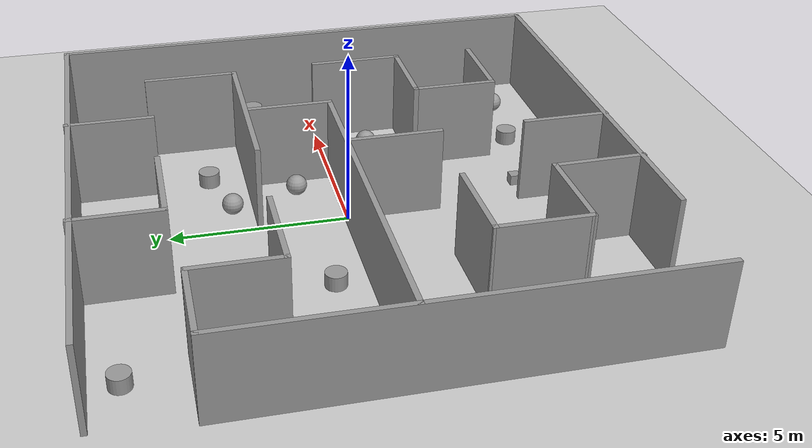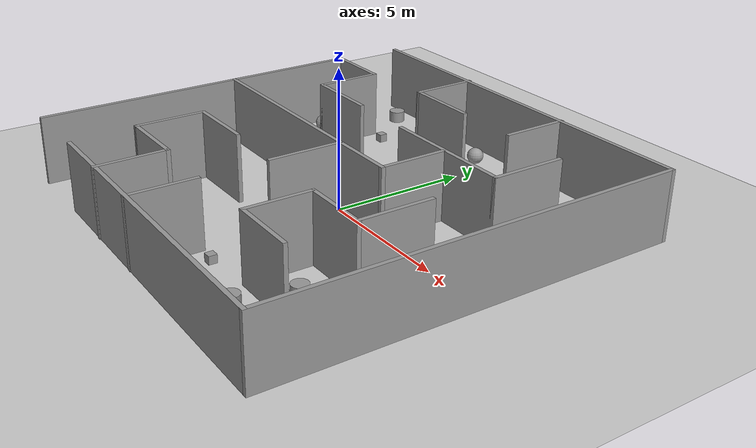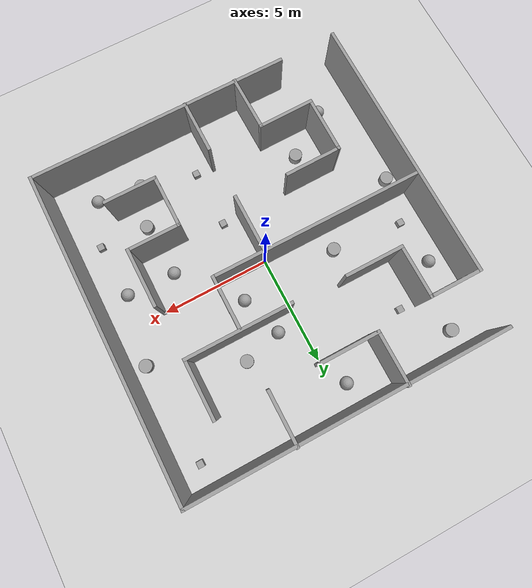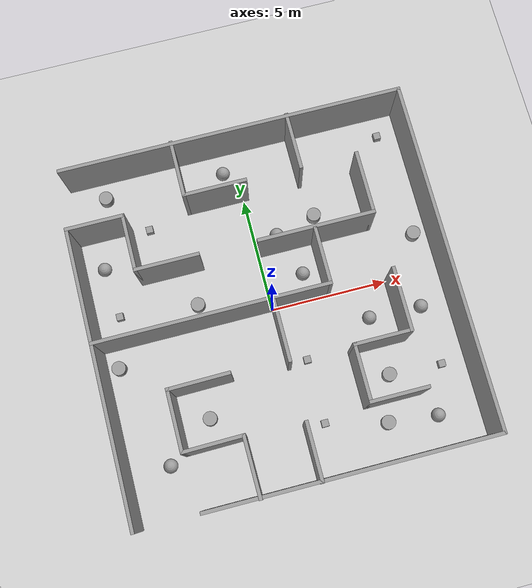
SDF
<?xml version="1.0"?>
<sdf version="1.4">
    <world name="default">
        <!-- A ground plane -->
        <include>
            <uri>model://ground_plane</uri>
        </include>

         <!-- A light source -->
        <include>
            <uri>model://sun</uri>
        </include>

        <!-- Custom world -->
        <include>
            <uri>model://task3_floor</uri>
        </include>
    </world>
</sdf>

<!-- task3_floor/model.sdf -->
<sdf version='1.6'>
  <model name='task3_floor'>
    <link name='Wall_0'>
      <pose frame=''>-7.41127 -1.29055 0 0 -0 1.5708</pose>
      <self_collide>0</self_collide>
      <enable_wind>0</enable_wind>
      <kinematic>0</kinematic>
      <visual name='Wall_0_Visual'>
        <pose frame=''>0 0 1.25 0 -0 0</pose>
        <geometry>
          <box>
            <size>12.5 0.15 2.5</size>
          </box>
        </geometry>
        <material>
          <script>
            <uri>file://media/materials/scripts/gazebo.material</uri>
            <name>Gazebo/Grey</name>
          </script>
          <ambient>1 1 1 1</ambient>
        </material>
        <meta>
          <layer>0</layer>
        </meta>
        <transparency>0</transparency>
        <cast_shadows>1</cast_shadows>
      </visual>
      <collision name='Wall_0_Collision'>
        <laser_retro>0</laser_retro>
        <max_contacts>10</max_contacts>
        <pose frame=''>0 0 1.25 0 -0 0</pose>
        <geometry>
          <box>
            <size>12.5 0.15 2.5</size>
          </box>
        </geometry>
        <surface>
          <friction>
            <ode>
              <mu>1</mu>
              <mu2>1</mu2>
              <fdir1>0 0 0</fdir1>
              <slip1>0</slip1>
              <slip2>0</slip2>
            </ode>
            <torsional>
              <coefficient>1</coefficient>
              <patch_radius>0</patch_radius>
              <surface_radius>0</surface_radius>
              <use_patch_radius>1</use_patch_radius>
              <ode>
                <slip>0</slip>
              </ode>
            </torsional>
          </friction>
          <bounce>
            <restitution_coefficient>0</restitution_coefficient>
            <threshold>1e+06</threshold>
          </bounce>
          <contact>
            <collide_without_contact>0</collide_without_contact>
            <collide_without_contact_bitmask>1</collide_without_contact_bitmask>
            <collide_bitmask>1</collide_bitmask>
            <ode>
              <soft_cfm>0</soft_cfm>
              <soft_erp>0.2</soft_erp>
              <kp>1e+13</kp>
              <kd>1</kd>
              <max_vel>0.01</max_vel>
              <min_depth>0</min_depth>
            </ode>
            <bullet>
              <split_impulse>1</split_impulse>
              <split_impulse_penetration_threshold>-0.01</split_impulse_penetration_threshold>
              <soft_cfm>0</soft_cfm>
              <soft_erp>0.2</soft_erp>
              <kp>1e+13</kp>
              <kd>1</kd>
            </bullet>
          </contact>
        </surface>
      </collision>
    </link>
    <link name='Wall_1'>
      <pose frame=''>-6.23627 4.88445 0 0 -0 0</pose>
      <self_collide>0</self_collide>
      <enable_wind>0</enable_wind>
      <kinematic>0</kinematic>
      <visual name='Wall_1_Visual'>
        <pose frame=''>0 0 1.25 0 -0 0</pose>
        <geometry>
          <box>
            <size>2.5 0.15 2.5</size>
          </box>
        </geometry>
        <material>
          <script>
            <uri>file://media/materials/scripts/gazebo.material</uri>
            <name>Gazebo/Grey</name>
          </script>
          <ambient>1 1 1 1</ambient>
        </material>
        <meta>
          <layer>0</layer>
        </meta>
        <transparency>0</transparency>
        <cast_shadows>1</cast_shadows>
      </visual>
      <collision name='Wall_1_Collision'>
        <laser_retro>0</laser_retro>
        <max_contacts>10</max_contacts>
        <pose frame=''>0 0 1.25 0 -0 0</pose>
        <geometry>
          <box>
            <size>2.5 0.15 2.5</size>
          </box>
        </geometry>
        <surface>
          <friction>
            <ode>
              <mu>1</mu>
              <mu2>1</mu2>
              <fdir1>0 0 0</fdir1>
              <slip1>0</slip1>
              <slip2>0</slip2>
            </ode>
            <torsional>
              <coefficient>1</coefficient>
              <patch_radius>0</patch_radius>
              <surface_radius>0</surface_radius>
              <use_patch_radius>1</use_patch_radius>
              <ode>
                <slip>0</slip>
              </ode>
            </torsional>
          </friction>
          <bounce>
            <restitution_coefficient>0</restitution_coefficient>
            <threshold>1e+06</threshold>
          </bounce>
          <contact>
            <collide_without_contact>0</collide_without_contact>
            <collide_without_contact_bitmask>1</collide_without_contact_bitmask>
            <collide_bitmask>1</collide_bitmask>
            <ode>
              <soft_cfm>0</soft_cfm>
              <soft_erp>0.2</soft_erp>
              <kp>1e+13</kp>
              <kd>1</kd>
              <max_vel>0.01</max_vel>
              <min_depth>0</min_depth>
            </ode>
            <bullet>
              <split_impulse>1</split_impulse>
              <split_impulse_penetration_threshold>-0.01</split_impulse_penetration_threshold>
              <soft_cfm>0</soft_cfm>
              <soft_erp>0.2</soft_erp>
              <kp>1e+13</kp>
              <kd>1</kd>
            </bullet>
          </contact>
        </surface>
      </collision>
    </link>
    <link name='Wall_11'>
      <pose frame=''>0.05275 -1.30154 0 0 0 -1.5708</pose>
      <self_collide>0</self_collide>
      <enable_wind>0</enable_wind>
      <kinematic>0</kinematic>
      <visual name='Wall_11_Visual'>
        <pose frame=''>0 0 1.25 0 -0 0</pose>
        <geometry>
          <box>
            <size>2.75 0.15 2.5</size>
          </box>
        </geometry>
        <material>
          <script>
            <uri>file://media/materials/scripts/gazebo.material</uri>
            <name>Gazebo/Grey</name>
          </script>
          <ambient>1 1 1 1</ambient>
        </material>
        <meta>
          <layer>0</layer>
        </meta>
        <transparency>0</transparency>
        <cast_shadows>1</cast_shadows>
      </visual>
      <collision name='Wall_11_Collision'>
        <laser_retro>0</laser_retro>
        <max_contacts>10</max_contacts>
        <pose frame=''>0 0 1.25 0 -0 0</pose>
        <geometry>
          <box>
            <size>2.75 0.15 2.5</size>
          </box>
        </geometry>
        <surface>
          <friction>
            <ode>
              <mu>1</mu>
              <mu2>1</mu2>
              <fdir1>0 0 0</fdir1>
              <slip1>0</slip1>
              <slip2>0</slip2>
            </ode>
            <torsional>
              <coefficient>1</coefficient>
              <patch_radius>0</patch_radius>
              <surface_radius>0</surface_radius>
              <use_patch_radius>1</use_patch_radius>
              <ode>
                <slip>0</slip>
              </ode>
            </torsional>
          </friction>
          <bounce>
            <restitution_coefficient>0</restitution_coefficient>
            <threshold>1e+06</threshold>
          </bounce>
          <contact>
            <collide_without_contact>0</collide_without_contact>
            <collide_without_contact_bitmask>1</collide_without_contact_bitmask>
            <collide_bitmask>1</collide_bitmask>
            <ode>
              <soft_cfm>0</soft_cfm>
              <soft_erp>0.2</soft_erp>
              <kp>1e+13</kp>
              <kd>1</kd>
              <max_vel>0.01</max_vel>
              <min_depth>0</min_depth>
            </ode>
            <bullet>
              <split_impulse>1</split_impulse>
              <split_impulse_penetration_threshold>-0.01</split_impulse_penetration_threshold>
              <soft_cfm>0</soft_cfm>
              <soft_erp>0.2</soft_erp>
              <kp>1e+13</kp>
              <kd>1</kd>
            </bullet>
          </contact>
        </surface>
      </collision>
    </link>
    <link name='Wall_13'>
      <pose frame=''>-3.64867 -2.49464 0 0 0 -3.1294</pose>
      <self_collide>0</self_collide>
      <enable_wind>0</enable_wind>
      <kinematic>0</kinematic>
      <visual name='Wall_13_Visual'>
        <pose frame=''>0 0 1.25 0 -0 0</pose>
        <geometry>
          <box>
            <size>2.65858 0.15 2.5</size>
          </box>
        </geometry>
        <material>
          <script>
            <uri>file://media/materials/scripts/gazebo.material</uri>
            <name>Gazebo/Grey</name>
          </script>
          <ambient>1 1 1 1</ambient>
        </material>
        <meta>
          <layer>0</layer>
        </meta>
        <transparency>0</transparency>
        <cast_shadows>1</cast_shadows>
      </visual>
      <collision name='Wall_13_Collision'>
        <laser_retro>0</laser_retro>
        <max_contacts>10</max_contacts>
        <pose frame=''>0 0 1.25 0 -0 0</pose>
        <geometry>
          <box>
            <size>2.65858 0.15 2.5</size>
          </box>
        </geometry>
        <surface>
          <friction>
            <ode>
              <mu>1</mu>
              <mu2>1</mu2>
              <fdir1>0 0 0</fdir1>
              <slip1>0</slip1>
              <slip2>0</slip2>
            </ode>
            <torsional>
              <coefficient>1</coefficient>
              <patch_radius>0</patch_radius>
              <surface_radius>0</surface_radius>
              <use_patch_radius>1</use_patch_radius>
              <ode>
                <slip>0</slip>
              </ode>
            </torsional>
          </friction>
          <bounce>
            <restitution_coefficient>0</restitution_coefficient>
            <threshold>1e+06</threshold>
          </bounce>
          <contact>
            <collide_without_contact>0</collide_without_contact>
            <collide_without_contact_bitmask>1</collide_without_contact_bitmask>
            <collide_bitmask>1</collide_bitmask>
            <ode>
              <soft_cfm>0</soft_cfm>
              <soft_erp>0.2</soft_erp>
              <kp>1e+13</kp>
              <kd>1</kd>
              <max_vel>0.01</max_vel>
              <min_depth>0</min_depth>
            </ode>
            <bullet>
              <split_impulse>1</split_impulse>
              <split_impulse_penetration_threshold>-0.01</split_impulse_penetration_threshold>
              <soft_cfm>0</soft_cfm>
              <soft_erp>0.2</soft_erp>
              <kp>1e+13</kp>
              <kd>1</kd>
            </bullet>
          </contact>
        </surface>
      </collision>
    </link>
    <link name='Wall_14'>
      <pose frame=''>-4.90287 -3.76414 0 0 0 -1.5708</pose>
      <self_collide>0</self_collide>
      <enable_wind>0</enable_wind>
      <kinematic>0</kinematic>
      <visual name='Wall_14_Visual'>
        <pose frame=''>0 0 1.25 0 -0 0</pose>
        <geometry>
          <box>
            <size>2.6584 0.15 2.5</size>
          </box>
        </geometry>
        <material>
          <script>
            <uri>file://media/materials/scripts/gazebo.material</uri>
            <name>Gazebo/Grey</name>
          </script>
          <ambient>1 1 1 1</ambient>
        </material>
        <meta>
          <layer>0</layer>
        </meta>
        <transparency>0</transparency>
        <cast_shadows>1</cast_shadows>
      </visual>
      <collision name='Wall_14_Collision'>
        <laser_retro>0</laser_retro>
        <max_contacts>10</max_contacts>
        <pose frame=''>0 0 1.25 0 -0 0</pose>
        <geometry>
          <box>
            <size>2.6584 0.15 2.5</size>
          </box>
        </geometry>
        <surface>
          <friction>
            <ode>
              <mu>1</mu>
              <mu2>1</mu2>
              <fdir1>0 0 0</fdir1>
              <slip1>0</slip1>
              <slip2>0</slip2>
            </ode>
            <torsional>
              <coefficient>1</coefficient>
              <patch_radius>0</patch_radius>
              <surface_radius>0</surface_radius>
              <use_patch_radius>1</use_patch_radius>
              <ode>
                <slip>0</slip>
              </ode>
            </torsional>
          </friction>
          <bounce>
            <restitution_coefficient>0</restitution_coefficient>
            <threshold>1e+06</threshold>
          </bounce>
          <contact>
            <collide_without_contact>0</collide_without_contact>
            <collide_without_contact_bitmask>1</collide_without_contact_bitmask>
            <collide_bitmask>1</collide_bitmask>
            <ode>
              <soft_cfm>0</soft_cfm>
              <soft_erp>0.2</soft_erp>
              <kp>1e+13</kp>
              <kd>1</kd>
              <max_vel>0.01</max_vel>
              <min_depth>0</min_depth>
            </ode>
            <bullet>
              <split_impulse>1</split_impulse>
              <split_impulse_penetration_threshold>-0.01</split_impulse_penetration_threshold>
              <soft_cfm>0</soft_cfm>
              <soft_erp>0.2</soft_erp>
              <kp>1e+13</kp>
              <kd>1</kd>
            </bullet>
          </contact>
        </surface>
      </collision>
    </link>
    <link name='Wall_15'>
      <pose frame=''>-3.66396 -5.00304 0 0 -0 0.012345</pose>
      <self_collide>0</self_collide>
      <enable_wind>0</enable_wind>
      <kinematic>0</kinematic>
      <visual name='Wall_15_Visual'>
        <pose frame=''>0 0 1.25 0 -0 0</pose>
        <geometry>
          <box>
            <size>2.628 0.15 2.5</size>
          </box>
        </geometry>
        <material>
          <script>
            <uri>file://media/materials/scripts/gazebo.material</uri>
            <name>Gazebo/Grey</name>
          </script>
          <ambient>1 1 1 1</ambient>
        </material>
        <meta>
          <layer>0</layer>
        </meta>
        <transparency>0</transparency>
        <cast_shadows>1</cast_shadows>
      </visual>
      <collision name='Wall_15_Collision'>
        <laser_retro>0</laser_retro>
        <max_contacts>10</max_contacts>
        <pose frame=''>0 0 1.25 0 -0 0</pose>
        <geometry>
          <box>
            <size>2.628 0.15 2.5</size>
          </box>
        </geometry>
        <surface>
          <friction>
            <ode>
              <mu>1</mu>
              <mu2>1</mu2>
              <fdir1>0 0 0</fdir1>
              <slip1>0</slip1>
              <slip2>0</slip2>
            </ode>
            <torsional>
              <coefficient>1</coefficient>
              <patch_radius>0</patch_radius>
              <surface_radius>0</surface_radius>
              <use_patch_radius>1</use_patch_radius>
              <ode>
                <slip>0</slip>
              </ode>
            </torsional>
          </friction>
          <bounce>
            <restitution_coefficient>0</restitution_coefficient>
            <threshold>1e+06</threshold>
          </bounce>
          <contact>
            <collide_without_contact>0</collide_without_contact>
            <collide_without_contact_bitmask>1</collide_without_contact_bitmask>
            <collide_bitmask>1</collide_bitmask>
            <ode>
              <soft_cfm>0</soft_cfm>
              <soft_erp>0.2</soft_erp>
              <kp>1e+13</kp>
              <kd>1</kd>
              <max_vel>0.01</max_vel>
              <min_depth>0</min_depth>
            </ode>
            <bullet>
              <split_impulse>1</split_impulse>
              <split_impulse_penetration_threshold>-0.01</split_impulse_penetration_threshold>
              <soft_cfm>0</soft_cfm>
              <soft_erp>0.2</soft_erp>
              <kp>1e+13</kp>
              <kd>1</kd>
            </bullet>
          </contact>
        </surface>
      </collision>
    </link>
    <link name='Wall_16'>
      <pose frame=''>-2.40976 -6.22665 0 0 0 -1.55845</pose>
      <self_collide>0</self_collide>
      <enable_wind>0</enable_wind>
      <kinematic>0</kinematic>
      <visual name='Wall_16_Visual'>
        <pose frame=''>0 0 1.25 0 -0 0</pose>
        <geometry>
          <box>
            <size>2.628 0.15 2.5</size>
          </box>
        </geometry>
        <material>
          <script>
            <uri>file://media/materials/scripts/gazebo.material</uri>
            <name>Gazebo/Grey</name>
          </script>
          <ambient>1 1 1 1</ambient>
        </material>
        <meta>
          <layer>0</layer>
        </meta>
        <transparency>0</transparency>
        <cast_shadows>1</cast_shadows>
      </visual>
      <collision name='Wall_16_Collision'>
        <laser_retro>0</laser_retro>
        <max_contacts>10</max_contacts>
        <pose frame=''>0 0 1.25 0 -0 0</pose>
        <geometry>
          <box>
            <size>2.628 0.15 2.5</size>
          </box>
        </geometry>
        <surface>
          <friction>
            <ode>
              <mu>1</mu>
              <mu2>1</mu2>
              <fdir1>0 0 0</fdir1>
              <slip1>0</slip1>
              <slip2>0</slip2>
            </ode>
            <torsional>
              <coefficient>1</coefficient>
              <patch_radius>0</patch_radius>
              <surface_radius>0</surface_radius>
              <use_patch_radius>1</use_patch_radius>
              <ode>
                <slip>0</slip>
              </ode>
            </torsional>
          </friction>
          <bounce>
            <restitution_coefficient>0</restitution_coefficient>
            <threshold>1e+06</threshold>
          </bounce>
          <contact>
            <collide_without_contact>0</collide_without_contact>
            <collide_without_contact_bitmask>1</collide_without_contact_bitmask>
            <collide_bitmask>1</collide_bitmask>
            <ode>
              <soft_cfm>0</soft_cfm>
              <soft_erp>0.2</soft_erp>
              <kp>1e+13</kp>
              <kd>1</kd>
              <max_vel>0.01</max_vel>
              <min_depth>0</min_depth>
            </ode>
            <bullet>
              <split_impulse>1</split_impulse>
              <split_impulse_penetration_threshold>-0.01</split_impulse_penetration_threshold>
              <soft_cfm>0</soft_cfm>
              <soft_erp>0.2</soft_erp>
              <kp>1e+13</kp>
              <kd>1</kd>
            </bullet>
          </contact>
        </surface>
      </collision>
    </link>
    <link name='Wall_18'>
      <pose frame=''>1.36126 -7.43496 0 0 -0 0</pose>
      <self_collide>0</self_collide>
      <enable_wind>0</enable_wind>
      <kinematic>0</kinematic>
      <visual name='Wall_18_Visual'>
        <pose frame=''>0 0 1.25 0 -0 0</pose>
        <geometry>
          <box>
            <size>12.25 0.15 2.5</size>
          </box>
        </geometry>
        <material>
          <script>
            <uri>file://media/materials/scripts/gazebo.material</uri>
            <name>Gazebo/Grey</name>
          </script>
          <ambient>1 1 1 1</ambient>
        </material>
        <meta>
          <layer>0</layer>
        </meta>
        <transparency>0</transparency>
        <cast_shadows>1</cast_shadows>
      </visual>
      <collision name='Wall_18_Collision'>
        <laser_retro>0</laser_retro>
        <max_contacts>10</max_contacts>
        <pose frame=''>0 0 1.25 0 -0 0</pose>
        <geometry>
          <box>
            <size>12.25 0.15 2.5</size>
          </box>
        </geometry>
        <surface>
          <friction>
            <ode>
              <mu>1</mu>
              <mu2>1</mu2>
              <fdir1>0 0 0</fdir1>
              <slip1>0</slip1>
              <slip2>0</slip2>
            </ode>
            <torsional>
              <coefficient>1</coefficient>
              <patch_radius>0</patch_radius>
              <surface_radius>0</surface_radius>
              <use_patch_radius>1</use_patch_radius>
              <ode>
                <slip>0</slip>
              </ode>
            </torsional>
          </friction>
          <bounce>
            <restitution_coefficient>0</restitution_coefficient>
            <threshold>1e+06</threshold>
          </bounce>
          <contact>
            <collide_without_contact>0</collide_without_contact>
            <collide_without_contact_bitmask>1</collide_without_contact_bitmask>
            <collide_bitmask>1</collide_bitmask>
            <ode>
              <soft_cfm>0</soft_cfm>
              <soft_erp>0.2</soft_erp>
              <kp>1e+13</kp>
              <kd>1</kd>
              <max_vel>0.01</max_vel>
              <min_depth>0</min_depth>
            </ode>
            <bullet>
              <split_impulse>1</split_impulse>
              <split_impulse_penetration_threshold>-0.01</split_impulse_penetration_threshold>
              <soft_cfm>0</soft_cfm>
              <soft_erp>0.2</soft_erp>
              <kp>1e+13</kp>
              <kd>1</kd>
            </bullet>
          </contact>
        </surface>
      </collision>
    </link>
    <link name='Wall_19'>
      <pose frame=''>7.41127 -0.009962 0 0 -0 1.5708</pose>
      <self_collide>0</self_collide>
      <enable_wind>0</enable_wind>
      <kinematic>0</kinematic>
      <visual name='Wall_19_Visual'>
        <pose frame=''>0 0 1.25 0 -0 0</pose>
        <geometry>
          <box>
            <size>15 0.15 2.5</size>
          </box>
        </geometry>
        <material>
          <script>
            <uri>file://media/materials/scripts/gazebo.material</uri>
            <name>Gazebo/Grey</name>
          </script>
          <ambient>1 1 1 1</ambient>
        </material>
        <meta>
          <layer>0</layer>
        </meta>
        <transparency>0</transparency>
        <cast_shadows>1</cast_shadows>
      </visual>
      <collision name='Wall_19_Collision'>
        <laser_retro>0</laser_retro>
        <max_contacts>10</max_contacts>
        <pose frame=''>0 0 1.25 0 -0 0</pose>
        <geometry>
          <box>
            <size>15 0.15 2.5</size>
          </box>
        </geometry>
        <surface>
          <friction>
            <ode>
              <mu>1</mu>
              <mu2>1</mu2>
              <fdir1>0 0 0</fdir1>
              <slip1>0</slip1>
              <slip2>0</slip2>
            </ode>
            <torsional>
              <coefficient>1</coefficient>
              <patch_radius>0</patch_radius>
              <surface_radius>0</surface_radius>
              <use_patch_radius>1</use_patch_radius>
              <ode>
                <slip>0</slip>
              </ode>
            </torsional>
          </friction>
          <bounce>
            <restitution_coefficient>0</restitution_coefficient>
            <threshold>1e+06</threshold>
          </bounce>
          <contact>
            <collide_without_contact>0</collide_without_contact>
            <collide_without_contact_bitmask>1</collide_without_contact_bitmask>
            <collide_bitmask>1</collide_bitmask>
            <ode>
              <soft_cfm>0</soft_cfm>
              <soft_erp>0.2</soft_erp>
              <kp>1e+13</kp>
              <kd>1</kd>
              <max_vel>0.01</max_vel>
              <min_depth>0</min_depth>
            </ode>
            <bullet>
              <split_impulse>1</split_impulse>
              <split_impulse_penetration_threshold>-0.01</split_impulse_penetration_threshold>
              <soft_cfm>0</soft_cfm>
              <soft_erp>0.2</soft_erp>
              <kp>1e+13</kp>
              <kd>1</kd>
            </bullet>
          </contact>
        </surface>
      </collision>
    </link>
    <link name='Wall_2'>
      <pose frame=''>-5.06126 3.70945 0 0 0 -1.5708</pose>
      <self_collide>0</self_collide>
      <enable_wind>0</enable_wind>
      <kinematic>0</kinematic>
      <visual name='Wall_2_Visual'>
        <pose frame=''>0 0 1.25 0 -0 0</pose>
        <geometry>
          <box>
            <size>2.5 0.15 2.5</size>
          </box>
        </geometry>
        <material>
          <script>
            <uri>file://media/materials/scripts/gazebo.material</uri>
            <name>Gazebo/Grey</name>
          </script>
          <ambient>1 1 1 1</ambient>
        </material>
        <meta>
          <layer>0</layer>
        </meta>
        <transparency>0</transparency>
        <cast_shadows>1</cast_shadows>
      </visual>
      <collision name='Wall_2_Collision'>
        <laser_retro>0</laser_retro>
        <max_contacts>10</max_contacts>
        <pose frame=''>0 0 1.25 0 -0 0</pose>
        <geometry>
          <box>
            <size>2.5 0.15 2.5</size>
          </box>
        </geometry>
        <surface>
          <friction>
            <ode>
              <mu>1</mu>
              <mu2>1</mu2>
              <fdir1>0 0 0</fdir1>
              <slip1>0</slip1>
              <slip2>0</slip2>
            </ode>
            <torsional>
              <coefficient>1</coefficient>
              <patch_radius>0</patch_radius>
              <surface_radius>0</surface_radius>
              <use_patch_radius>1</use_patch_radius>
              <ode>
                <slip>0</slip>
              </ode>
            </torsional>
          </friction>
          <bounce>
            <restitution_coefficient>0</restitution_coefficient>
            <threshold>1e+06</threshold>
          </bounce>
          <contact>
            <collide_without_contact>0</collide_without_contact>
            <collide_without_contact_bitmask>1</collide_without_contact_bitmask>
            <collide_bitmask>1</collide_bitmask>
            <ode>
              <soft_cfm>0</soft_cfm>
              <soft_erp>0.2</soft_erp>
              <kp>1e+13</kp>
              <kd>1</kd>
              <max_vel>0.01</max_vel>
              <min_depth>0</min_depth>
            </ode>
            <bullet>
              <split_impulse>1</split_impulse>
              <split_impulse_penetration_threshold>-0.01</split_impulse_penetration_threshold>
              <soft_cfm>0</soft_cfm>
              <soft_erp>0.2</soft_erp>
              <kp>1e+13</kp>
              <kd>1</kd>
            </bullet>
          </contact>
        </surface>
      </collision>
    </link>
    <link name='Wall_20'>
      <pose frame=''>0.111265 7.41504 0 0 -0 3.14159</pose>
      <self_collide>0</self_collide>
      <enable_wind>0</enable_wind>
      <kinematic>0</kinematic>
      <visual name='Wall_20_Visual'>
        <pose frame=''>0 0 1.25 0 -0 0</pose>
        <geometry>
          <box>
            <size>14.75 0.15 2.5</size>
          </box>
        </geometry>
        <material>
          <script>
            <uri>file://media/materials/scripts/gazebo.material</uri>
            <name>Gazebo/Grey</name>
          </script>
          <ambient>1 1 1 1</ambient>
        </material>
        <meta>
          <layer>0</layer>
        </meta>
        <transparency>0</transparency>
        <cast_shadows>1</cast_shadows>
      </visual>
      <collision name='Wall_20_Collision'>
        <laser_retro>0</laser_retro>
        <max_contacts>10</max_contacts>
        <pose frame=''>0 0 1.25 0 -0 0</pose>
        <geometry>
          <box>
            <size>14.75 0.15 2.5</size>
          </box>
        </geometry>
        <surface>
          <friction>
            <ode>
              <mu>1</mu>
              <mu2>1</mu2>
              <fdir1>0 0 0</fdir1>
              <slip1>0</slip1>
              <slip2>0</slip2>
            </ode>
            <torsional>
              <coefficient>1</coefficient>
              <patch_radius>0</patch_radius>
              <surface_radius>0</surface_radius>
              <use_patch_radius>1</use_patch_radius>
              <ode>
                <slip>0</slip>
              </ode>
            </torsional>
          </friction>
          <bounce>
            <restitution_coefficient>0</restitution_coefficient>
            <threshold>1e+06</threshold>
          </bounce>
          <contact>
            <collide_without_contact>0</collide_without_contact>
            <collide_without_contact_bitmask>1</collide_without_contact_bitmask>
            <collide_bitmask>1</collide_bitmask>
            <ode>
              <soft_cfm>0</soft_cfm>
              <soft_erp>0.2</soft_erp>
              <kp>1e+13</kp>
              <kd>1</kd>
              <max_vel>0.01</max_vel>
              <min_depth>0</min_depth>
            </ode>
            <bullet>
              <split_impulse>1</split_impulse>
              <split_impulse_penetration_threshold>-0.01</split_impulse_penetration_threshold>
              <soft_cfm>0</soft_cfm>
              <soft_erp>0.2</soft_erp>
              <kp>1e+13</kp>
              <kd>1</kd>
            </bullet>
          </contact>
        </surface>
      </collision>
    </link>
    <link name='Wall_22'>
      <pose frame=''>-2.42903 6.29147 0 0 0 -1.5708</pose>
      <self_collide>0</self_collide>
      <enable_wind>0</enable_wind>
      <kinematic>0</kinematic>
      <visual name='Wall_22_Visual'>
        <pose frame=''>0 0 1.25 0 -0 0</pose>
        <geometry>
          <box>
            <size>2.5 0.15 2.5</size>
          </box>
        </geometry>
        <material>
          <script>
            <uri>file://media/materials/scripts/gazebo.material</uri>
            <name>Gazebo/Grey</name>
          </script>
          <ambient>1 1 1 1</ambient>
        </material>
        <meta>
          <layer>0</layer>
        </meta>
        <transparency>0</transparency>
        <cast_shadows>1</cast_shadows>
      </visual>
      <collision name='Wall_22_Collision'>
        <laser_retro>0</laser_retro>
        <max_contacts>10</max_contacts>
        <pose frame=''>0 0 1.25 0 -0 0</pose>
        <geometry>
          <box>
            <size>2.5 0.15 2.5</size>
          </box>
        </geometry>
        <surface>
          <friction>
            <ode>
              <mu>1</mu>
              <mu2>1</mu2>
              <fdir1>0 0 0</fdir1>
              <slip1>0</slip1>
              <slip2>0</slip2>
            </ode>
            <torsional>
              <coefficient>1</coefficient>
              <patch_radius>0</patch_radius>
              <surface_radius>0</surface_radius>
              <use_patch_radius>1</use_patch_radius>
              <ode>
                <slip>0</slip>
              </ode>
            </torsional>
          </friction>
          <bounce>
            <restitution_coefficient>0</restitution_coefficient>
            <threshold>1e+06</threshold>
          </bounce>
          <contact>
            <collide_without_contact>0</collide_without_contact>
            <collide_without_contact_bitmask>1</collide_without_contact_bitmask>
            <collide_bitmask>1</collide_bitmask>
            <ode>
              <soft_cfm>0</soft_cfm>
              <soft_erp>0.2</soft_erp>
              <kp>1e+13</kp>
              <kd>1</kd>
              <max_vel>0.01</max_vel>
              <min_depth>0</min_depth>
            </ode>
            <bullet>
              <split_impulse>1</split_impulse>
              <split_impulse_penetration_threshold>-0.01</split_impulse_penetration_threshold>
              <soft_cfm>0</soft_cfm>
              <soft_erp>0.2</soft_erp>
              <kp>1e+13</kp>
              <kd>1</kd>
            </bullet>
          </contact>
        </surface>
      </collision>
    </link>
    <link name='Wall_23'>
      <pose frame=''>-1.12903 5.11647 0 0 -0 0</pose>
      <self_collide>0</self_collide>
      <enable_wind>0</enable_wind>
      <kinematic>0</kinematic>
      <visual name='Wall_23_Visual'>
        <pose frame=''>0 0 1.25 0 -0 0</pose>
        <geometry>
          <box>
            <size>2.75 0.15 2.5</size>
          </box>
        </geometry>
        <material>
          <script>
            <uri>file://media/materials/scripts/gazebo.material</uri>
            <name>Gazebo/Grey</name>
          </script>
          <ambient>1 1 1 1</ambient>
        </material>
        <meta>
          <layer>0</layer>
        </meta>
        <transparency>0</transparency>
        <cast_shadows>1</cast_shadows>
      </visual>
      <collision name='Wall_23_Collision'>
        <laser_retro>0</laser_retro>
        <max_contacts>10</max_contacts>
        <pose frame=''>0 0 1.25 0 -0 0</pose>
        <geometry>
          <box>
            <size>2.75 0.15 2.5</size>
          </box>
        </geometry>
        <surface>
          <friction>
            <ode>
              <mu>1</mu>
              <mu2>1</mu2>
              <fdir1>0 0 0</fdir1>
              <slip1>0</slip1>
              <slip2>0</slip2>
            </ode>
            <torsional>
              <coefficient>1</coefficient>
              <patch_radius>0</patch_radius>
              <surface_radius>0</surface_radius>
              <use_patch_radius>1</use_patch_radius>
              <ode>
                <slip>0</slip>
              </ode>
            </torsional>
          </friction>
          <bounce>
            <restitution_coefficient>0</restitution_coefficient>
            <threshold>1e+06</threshold>
          </bounce>
          <contact>
            <collide_without_contact>0</collide_without_contact>
            <collide_without_contact_bitmask>1</collide_without_contact_bitmask>
            <collide_bitmask>1</collide_bitmask>
            <ode>
              <soft_cfm>0</soft_cfm>
              <soft_erp>0.2</soft_erp>
              <kp>1e+13</kp>
              <kd>1</kd>
              <max_vel>0.01</max_vel>
              <min_depth>0</min_depth>
            </ode>
            <bullet>
              <split_impulse>1</split_impulse>
              <split_impulse_penetration_threshold>-0.01</split_impulse_penetration_threshold>
              <soft_cfm>0</soft_cfm>
              <soft_erp>0.2</soft_erp>
              <kp>1e+13</kp>
              <kd>1</kd>
            </bullet>
          </contact>
        </surface>
      </collision>
    </link>
    <link name='Wall_25'>
      <pose frame=''>2.54822 6.27801 0 0 0 -1.5708</pose>
      <self_collide>0</self_collide>
      <enable_wind>0</enable_wind>
      <kinematic>0</kinematic>
      <visual name='Wall_25_Visual'>
        <pose frame=''>0 0 1.25 0 -0 0</pose>
        <geometry>
          <box>
            <size>2.5 0.15 2.5</size>
          </box>
        </geometry>
        <material>
          <script>
            <uri>file://media/materials/scripts/gazebo.material</uri>
            <name>Gazebo/Grey</name>
          </script>
          <ambient>1 1 1 1</ambient>
        </material>
        <meta>
          <layer>0</layer>
        </meta>
        <transparency>0</transparency>
        <cast_shadows>1</cast_shadows>
      </visual>
      <collision name='Wall_25_Collision'>
        <laser_retro>0</laser_retro>
        <max_contacts>10</max_contacts>
        <pose frame=''>0 0 1.25 0 -0 0</pose>
        <geometry>
          <box>
            <size>2.5 0.15 2.5</size>
          </box>
        </geometry>
        <surface>
          <friction>
            <ode>
              <mu>1</mu>
              <mu2>1</mu2>
              <fdir1>0 0 0</fdir1>
              <slip1>0</slip1>
              <slip2>0</slip2>
            </ode>
            <torsional>
              <coefficient>1</coefficient>
              <patch_radius>0</patch_radius>
              <surface_radius>0</surface_radius>
              <use_patch_radius>1</use_patch_radius>
              <ode>
                <slip>0</slip>
              </ode>
            </torsional>
          </friction>
          <bounce>
            <restitution_coefficient>0</restitution_coefficient>
            <threshold>1e+06</threshold>
          </bounce>
          <contact>
            <collide_without_contact>0</collide_without_contact>
            <collide_without_contact_bitmask>1</collide_without_contact_bitmask>
            <collide_bitmask>1</collide_bitmask>
            <ode>
              <soft_cfm>0</soft_cfm>
              <soft_erp>0.2</soft_erp>
              <kp>1e+13</kp>
              <kd>1</kd>
              <max_vel>0.01</max_vel>
              <min_depth>0</min_depth>
            </ode>
            <bullet>
              <split_impulse>1</split_impulse>
              <split_impulse_penetration_threshold>-0.01</split_impulse_penetration_threshold>
              <soft_cfm>0</soft_cfm>
              <soft_erp>0.2</soft_erp>
              <kp>1e+13</kp>
              <kd>1</kd>
            </bullet>
          </contact>
        </surface>
      </collision>
    </link>
    <link name='Wall_27'>
      <pose frame=''>5.05736 -1.3267 0 0 0 -1.5708</pose>
      <self_collide>0</self_collide>
      <enable_wind>0</enable_wind>
      <kinematic>0</kinematic>
      <visual name='Wall_27_Visual'>
        <pose frame=''>0 0 1.25 0 -0 0</pose>
        <geometry>
          <box>
            <size>2.75 0.15 2.5</size>
          </box>
        </geometry>
        <material>
          <script>
            <uri>file://media/materials/scripts/gazebo.material</uri>
            <name>Gazebo/Grey</name>
          </script>
          <ambient>1 1 1 1</ambient>
        </material>
        <meta>
          <layer>0</layer>
        </meta>
        <transparency>0</transparency>
        <cast_shadows>1</cast_shadows>
      </visual>
      <collision name='Wall_27_Collision'>
        <laser_retro>0</laser_retro>
        <max_contacts>10</max_contacts>
        <pose frame=''>0 0 1.25 0 -0 0</pose>
        <geometry>
          <box>
            <size>2.75 0.15 2.5</size>
          </box>
        </geometry>
        <surface>
          <friction>
            <ode>
              <mu>1</mu>
              <mu2>1</mu2>
              <fdir1>0 0 0</fdir1>
              <slip1>0</slip1>
              <slip2>0</slip2>
            </ode>
            <torsional>
              <coefficient>1</coefficient>
              <patch_radius>0</patch_radius>
              <surface_radius>0</surface_radius>
              <use_patch_radius>1</use_patch_radius>
              <ode>
                <slip>0</slip>
              </ode>
            </torsional>
          </friction>
          <bounce>
            <restitution_coefficient>0</restitution_coefficient>
            <threshold>1e+06</threshold>
          </bounce>
          <contact>
            <collide_without_contact>0</collide_without_contact>
            <collide_without_contact_bitmask>1</collide_without_contact_bitmask>
            <collide_bitmask>1</collide_bitmask>
            <ode>
              <soft_cfm>0</soft_cfm>
              <soft_erp>0.2</soft_erp>
              <kp>1e+13</kp>
              <kd>1</kd>
              <max_vel>0.01</max_vel>
              <min_depth>0</min_depth>
            </ode>
            <bullet>
              <split_impulse>1</split_impulse>
              <split_impulse_penetration_threshold>-0.01</split_impulse_penetration_threshold>
              <soft_cfm>0</soft_cfm>
              <soft_erp>0.2</soft_erp>
              <kp>1e+13</kp>
              <kd>1</kd>
            </bullet>
          </contact>
        </surface>
      </collision>
    </link>
    <link name='Wall_28'>
      <pose frame=''>3.88236 -2.6267 0 0 -0 3.14159</pose>
      <self_collide>0</self_collide>
      <enable_wind>0</enable_wind>
      <kinematic>0</kinematic>
      <visual name='Wall_28_Visual'>
        <pose frame=''>0 0 1.25 0 -0 0</pose>
        <geometry>
          <box>
            <size>2.5 0.15 2.5</size>
          </box>
        </geometry>
        <material>
          <script>
            <uri>file://media/materials/scripts/gazebo.material</uri>
            <name>Gazebo/Grey</name>
          </script>
          <ambient>1 1 1 1</ambient>
        </material>
        <meta>
          <layer>0</layer>
        </meta>
        <transparency>0</transparency>
        <cast_shadows>1</cast_shadows>
      </visual>
      <collision name='Wall_28_Collision'>
        <laser_retro>0</laser_retro>
        <max_contacts>10</max_contacts>
        <pose frame=''>0 0 1.25 0 -0 0</pose>
        <geometry>
          <box>
            <size>2.5 0.15 2.5</size>
          </box>
        </geometry>
        <surface>
          <friction>
            <ode>
              <mu>1</mu>
              <mu2>1</mu2>
              <fdir1>0 0 0</fdir1>
              <slip1>0</slip1>
              <slip2>0</slip2>
            </ode>
            <torsional>
              <coefficient>1</coefficient>
              <patch_radius>0</patch_radius>
              <surface_radius>0</surface_radius>
              <use_patch_radius>1</use_patch_radius>
              <ode>
                <slip>0</slip>
              </ode>
            </torsional>
          </friction>
          <bounce>
            <restitution_coefficient>0</restitution_coefficient>
            <threshold>1e+06</threshold>
          </bounce>
          <contact>
            <collide_without_contact>0</collide_without_contact>
            <collide_without_contact_bitmask>1</collide_without_contact_bitmask>
            <collide_bitmask>1</collide_bitmask>
            <ode>
              <soft_cfm>0</soft_cfm>
              <soft_erp>0.2</soft_erp>
              <kp>1e+13</kp>
              <kd>1</kd>
              <max_vel>0.01</max_vel>
              <min_depth>0</min_depth>
            </ode>
            <bullet>
              <split_impulse>1</split_impulse>
              <split_impulse_penetration_threshold>-0.01</split_impulse_penetration_threshold>
              <soft_cfm>0</soft_cfm>
              <soft_erp>0.2</soft_erp>
              <kp>1e+13</kp>
              <kd>1</kd>
            </bullet>
          </contact>
        </surface>
      </collision>
    </link>
    <link name='Wall_29'>
      <pose frame=''>2.70736 -3.8017 0 0 0 -1.5708</pose>
      <self_collide>0</self_collide>
      <enable_wind>0</enable_wind>
      <kinematic>0</kinematic>
      <visual name='Wall_29_Visual'>
        <pose frame=''>0 0 1.25 0 -0 0</pose>
        <geometry>
          <box>
            <size>2.5 0.15 2.5</size>
          </box>
        </geometry>
        <material>
          <script>
            <uri>file://media/materials/scripts/gazebo.material</uri>
            <name>Gazebo/Grey</name>
          </script>
          <ambient>1 1 1 1</ambient>
        </material>
        <meta>
          <layer>0</layer>
        </meta>
        <transparency>0</transparency>
        <cast_shadows>1</cast_shadows>
      </visual>
      <collision name='Wall_29_Collision'>
        <laser_retro>0</laser_retro>
        <max_contacts>10</max_contacts>
        <pose frame=''>0 0 1.25 0 -0 0</pose>
        <geometry>
          <box>
            <size>2.5 0.15 2.5</size>
          </box>
        </geometry>
        <surface>
          <friction>
            <ode>
              <mu>1</mu>
              <mu2>1</mu2>
              <fdir1>0 0 0</fdir1>
              <slip1>0</slip1>
              <slip2>0</slip2>
            </ode>
            <torsional>
              <coefficient>1</coefficient>
              <patch_radius>0</patch_radius>
              <surface_radius>0</surface_radius>
              <use_patch_radius>1</use_patch_radius>
              <ode>
                <slip>0</slip>
              </ode>
            </torsional>
          </friction>
          <bounce>
            <restitution_coefficient>0</restitution_coefficient>
            <threshold>1e+06</threshold>
          </bounce>
          <contact>
            <collide_without_contact>0</collide_without_contact>
            <collide_without_contact_bitmask>1</collide_without_contact_bitmask>
            <collide_bitmask>1</collide_bitmask>
            <ode>
              <soft_cfm>0</soft_cfm>
              <soft_erp>0.2</soft_erp>
              <kp>1e+13</kp>
              <kd>1</kd>
              <max_vel>0.01</max_vel>
              <min_depth>0</min_depth>
            </ode>
            <bullet>
              <split_impulse>1</split_impulse>
              <split_impulse_penetration_threshold>-0.01</split_impulse_penetration_threshold>
              <soft_cfm>0</soft_cfm>
              <soft_erp>0.2</soft_erp>
              <kp>1e+13</kp>
              <kd>1</kd>
            </bullet>
          </contact>
        </surface>
      </collision>
    </link>
    <link name='Wall_3'>
      <pose frame=''>-3.76126 2.53445 0 0 -0 0</pose>
      <self_collide>0</self_collide>
      <enable_wind>0</enable_wind>
      <kinematic>0</kinematic>
      <visual name='Wall_3_Visual'>
        <pose frame=''>0 0 1.25 0 -0 0</pose>
        <geometry>
          <box>
            <size>2.75 0.15 2.5</size>
          </box>
        </geometry>
        <material>
          <script>
            <uri>file://media/materials/scripts/gazebo.material</uri>
            <name>Gazebo/Grey</name>
          </script>
          <ambient>1 1 1 1</ambient>
        </material>
        <meta>
          <layer>0</layer>
        </meta>
        <transparency>0</transparency>
        <cast_shadows>1</cast_shadows>
      </visual>
      <collision name='Wall_3_Collision'>
        <laser_retro>0</laser_retro>
        <max_contacts>10</max_contacts>
        <pose frame=''>0 0 1.25 0 -0 0</pose>
        <geometry>
          <box>
            <size>2.75 0.15 2.5</size>
          </box>
        </geometry>
        <surface>
          <friction>
            <ode>
              <mu>1</mu>
              <mu2>1</mu2>
              <fdir1>0 0 0</fdir1>
              <slip1>0</slip1>
              <slip2>0</slip2>
            </ode>
            <torsional>
              <coefficient>1</coefficient>
              <patch_radius>0</patch_radius>
              <surface_radius>0</surface_radius>
              <use_patch_radius>1</use_patch_radius>
              <ode>
                <slip>0</slip>
              </ode>
            </torsional>
          </friction>
          <bounce>
            <restitution_coefficient>0</restitution_coefficient>
            <threshold>1e+06</threshold>
          </bounce>
          <contact>
            <collide_without_contact>0</collide_without_contact>
            <collide_without_contact_bitmask>1</collide_without_contact_bitmask>
            <collide_bitmask>1</collide_bitmask>
            <ode>
              <soft_cfm>0</soft_cfm>
              <soft_erp>0.2</soft_erp>
              <kp>1e+13</kp>
              <kd>1</kd>
              <max_vel>0.01</max_vel>
              <min_depth>0</min_depth>
            </ode>
            <bullet>
              <split_impulse>1</split_impulse>
              <split_impulse_penetration_threshold>-0.01</split_impulse_penetration_threshold>
              <soft_cfm>0</soft_cfm>
              <soft_erp>0.2</soft_erp>
              <kp>1e+13</kp>
              <kd>1</kd>
            </bullet>
          </contact>
        </surface>
      </collision>
    </link>
    <link name='Wall_30'>
      <pose frame=''>3.88236 -4.9767 0 0 -0 0</pose>
      <self_collide>0</self_collide>
      <enable_wind>0</enable_wind>
      <kinematic>0</kinematic>
      <visual name='Wall_30_Visual'>
        <pose frame=''>0 0 1.25 0 -0 0</pose>
        <geometry>
          <box>
            <size>2.5 0.15 2.5</size>
          </box>
        </geometry>
        <material>
          <script>
            <uri>file://media/materials/scripts/gazebo.material</uri>
            <name>Gazebo/Grey</name>
          </script>
          <ambient>1 1 1 1</ambient>
        </material>
        <meta>
          <layer>0</layer>
        </meta>
        <transparency>0</transparency>
        <cast_shadows>1</cast_shadows>
      </visual>
      <collision name='Wall_30_Collision'>
        <laser_retro>0</laser_retro>
        <max_contacts>10</max_contacts>
        <pose frame=''>0 0 1.25 0 -0 0</pose>
        <geometry>
          <box>
            <size>2.5 0.15 2.5</size>
          </box>
        </geometry>
        <surface>
          <friction>
            <ode>
              <mu>1</mu>
              <mu2>1</mu2>
              <fdir1>0 0 0</fdir1>
              <slip1>0</slip1>
              <slip2>0</slip2>
            </ode>
            <torsional>
              <coefficient>1</coefficient>
              <patch_radius>0</patch_radius>
              <surface_radius>0</surface_radius>
              <use_patch_radius>1</use_patch_radius>
              <ode>
                <slip>0</slip>
              </ode>
            </torsional>
          </friction>
          <bounce>
            <restitution_coefficient>0</restitution_coefficient>
            <threshold>1e+06</threshold>
          </bounce>
          <contact>
            <collide_without_contact>0</collide_without_contact>
            <collide_without_contact_bitmask>1</collide_without_contact_bitmask>
            <collide_bitmask>1</collide_bitmask>
            <ode>
              <soft_cfm>0</soft_cfm>
              <soft_erp>0.2</soft_erp>
              <kp>1e+13</kp>
              <kd>1</kd>
              <max_vel>0.01</max_vel>
              <min_depth>0</min_depth>
            </ode>
            <bullet>
              <split_impulse>1</split_impulse>
              <split_impulse_penetration_threshold>-0.01</split_impulse_penetration_threshold>
              <soft_cfm>0</soft_cfm>
              <soft_erp>0.2</soft_erp>
              <kp>1e+13</kp>
              <kd>1</kd>
            </bullet>
          </contact>
        </surface>
      </collision>
    </link>
    <link name='Wall_32'>
      <pose frame=''>0.067623 -6.27914 0 0 -0 1.5708</pose>
      <self_collide>0</self_collide>
      <enable_wind>0</enable_wind>
      <kinematic>0</kinematic>
      <visual name='Wall_32_Visual'>
        <pose frame=''>0 0 1.25 0 -0 0</pose>
        <geometry>
          <box>
            <size>2.5 0.15 2.5</size>
          </box>
        </geometry>
        <material>
          <script>
            <uri>file://media/materials/scripts/gazebo.material</uri>
            <name>Gazebo/Grey</name>
          </script>
          <ambient>1 1 1 1</ambient>
        </material>
        <meta>
          <layer>0</layer>
        </meta>
        <transparency>0</transparency>
        <cast_shadows>1</cast_shadows>
      </visual>
      <collision name='Wall_32_Collision'>
        <laser_retro>0</laser_retro>
        <max_contacts>10</max_contacts>
        <pose frame=''>0 0 1.25 0 -0 0</pose>
        <geometry>
          <box>
            <size>2.5 0.15 2.5</size>
          </box>
        </geometry>
        <surface>
          <friction>
            <ode>
              <mu>1</mu>
              <mu2>1</mu2>
              <fdir1>0 0 0</fdir1>
              <slip1>0</slip1>
              <slip2>0</slip2>
            </ode>
            <torsional>
              <coefficient>1</coefficient>
              <patch_radius>0</patch_radius>
              <surface_radius>0</surface_radius>
              <use_patch_radius>1</use_patch_radius>
              <ode>
                <slip>0</slip>
              </ode>
            </torsional>
          </friction>
          <bounce>
            <restitution_coefficient>0</restitution_coefficient>
            <threshold>1e+06</threshold>
          </bounce>
          <contact>
            <collide_without_contact>0</collide_without_contact>
            <collide_without_contact_bitmask>1</collide_without_contact_bitmask>
            <collide_bitmask>1</collide_bitmask>
            <ode>
              <soft_cfm>0</soft_cfm>
              <soft_erp>0.2</soft_erp>
              <kp>1e+13</kp>
              <kd>1</kd>
              <max_vel>0.01</max_vel>
              <min_depth>0</min_depth>
            </ode>
            <bullet>
              <split_impulse>1</split_impulse>
              <split_impulse_penetration_threshold>-0.01</split_impulse_penetration_threshold>
              <soft_cfm>0</soft_cfm>
              <soft_erp>0.2</soft_erp>
              <kp>1e+13</kp>
              <kd>1</kd>
            </bullet>
          </contact>
        </surface>
      </collision>
    </link>
    <link name='Wall_5'>
      <pose frame=''>2.50834 2.47627 0 0 -0 0</pose>
      <self_collide>0</self_collide>
      <enable_wind>0</enable_wind>
      <kinematic>0</kinematic>
      <visual name='Wall_5_Visual'>
        <pose frame=''>0 0 1.25 0 -0 0</pose>
        <geometry>
          <box>
            <size>5 0.15 2.5</size>
          </box>
        </geometry>
        <material>
          <script>
            <uri>file://media/materials/scripts/gazebo.material</uri>
            <name>Gazebo/Grey</name>
          </script>
          <ambient>1 1 1 1</ambient>
        </material>
        <meta>
          <layer>0</layer>
        </meta>
        <transparency>0</transparency>
        <cast_shadows>1</cast_shadows>
      </visual>
      <collision name='Wall_5_Collision'>
        <laser_retro>0</laser_retro>
        <max_contacts>10</max_contacts>
        <pose frame=''>0 0 1.25 0 -0 0</pose>
        <geometry>
          <box>
            <size>5 0.15 2.5</size>
          </box>
        </geometry>
        <surface>
          <friction>
            <ode>
              <mu>1</mu>
              <mu2>1</mu2>
              <fdir1>0 0 0</fdir1>
              <slip1>0</slip1>
              <slip2>0</slip2>
            </ode>
            <torsional>
              <coefficient>1</coefficient>
              <patch_radius>0</patch_radius>
              <surface_radius>0</surface_radius>
              <use_patch_radius>1</use_patch_radius>
              <ode>
                <slip>0</slip>
              </ode>
            </torsional>
          </friction>
          <bounce>
            <restitution_coefficient>0</restitution_coefficient>
            <threshold>1e+06</threshold>
          </bounce>
          <contact>
            <collide_without_contact>0</collide_without_contact>
            <collide_without_contact_bitmask>1</collide_without_contact_bitmask>
            <collide_bitmask>1</collide_bitmask>
            <ode>
              <soft_cfm>0</soft_cfm>
              <soft_erp>0.2</soft_erp>
              <kp>1e+13</kp>
              <kd>1</kd>
              <max_vel>0.01</max_vel>
              <min_depth>0</min_depth>
            </ode>
            <bullet>
              <split_impulse>1</split_impulse>
              <split_impulse_penetration_threshold>-0.01</split_impulse_penetration_threshold>
              <soft_cfm>0</soft_cfm>
              <soft_erp>0.2</soft_erp>
              <kp>1e+13</kp>
              <kd>1</kd>
            </bullet>
          </contact>
        </surface>
      </collision>
    </link>
    <link name='Wall_6'>
      <pose frame=''>4.93334 3.77627 0 0 -0 1.5708</pose>
      <self_collide>0</self_collide>
      <enable_wind>0</enable_wind>
      <kinematic>0</kinematic>
      <visual name='Wall_6_Visual'>
        <pose frame=''>0 0 1.25 0 -0 0</pose>
        <geometry>
          <box>
            <size>2.75 0.15 2.5</size>
          </box>
        </geometry>
        <material>
          <script>
            <uri>file://media/materials/scripts/gazebo.material</uri>
            <name>Gazebo/Grey</name>
          </script>
          <ambient>1 1 1 1</ambient>
        </material>
        <meta>
          <layer>0</layer>
        </meta>
        <transparency>0</transparency>
        <cast_shadows>1</cast_shadows>
      </visual>
      <collision name='Wall_6_Collision'>
        <laser_retro>0</laser_retro>
        <max_contacts>10</max_contacts>
        <pose frame=''>0 0 1.25 0 -0 0</pose>
        <geometry>
          <box>
            <size>2.75 0.15 2.5</size>
          </box>
        </geometry>
        <surface>
          <friction>
            <ode>
              <mu>1</mu>
              <mu2>1</mu2>
              <fdir1>0 0 0</fdir1>
              <slip1>0</slip1>
              <slip2>0</slip2>
            </ode>
            <torsional>
              <coefficient>1</coefficient>
              <patch_radius>0</patch_radius>
              <surface_radius>0</surface_radius>
              <use_patch_radius>1</use_patch_radius>
              <ode>
                <slip>0</slip>
              </ode>
            </torsional>
          </friction>
          <bounce>
            <restitution_coefficient>0</restitution_coefficient>
            <threshold>1e+06</threshold>
          </bounce>
          <contact>
            <collide_without_contact>0</collide_without_contact>
            <collide_without_contact_bitmask>1</collide_without_contact_bitmask>
            <collide_bitmask>1</collide_bitmask>
            <ode>
              <soft_cfm>0</soft_cfm>
              <soft_erp>0.2</soft_erp>
              <kp>1e+13</kp>
              <kd>1</kd>
              <max_vel>0.01</max_vel>
              <min_depth>0</min_depth>
            </ode>
            <bullet>
              <split_impulse>1</split_impulse>
              <split_impulse_penetration_threshold>-0.01</split_impulse_penetration_threshold>
              <soft_cfm>0</soft_cfm>
              <soft_erp>0.2</soft_erp>
              <kp>1e+13</kp>
              <kd>1</kd>
            </bullet>
          </contact>
        </surface>
      </collision>
    </link>
    <link name='Wall_8'>
      <pose frame=''>-2.48626 0.029054 0 0 -0 0</pose>
      <self_collide>0</self_collide>
      <enable_wind>0</enable_wind>
      <kinematic>0</kinematic>
      <visual name='Wall_8_Visual'>
        <pose frame=''>0 0 1.25 0 -0 0</pose>
        <geometry>
          <box>
            <size>10 0.15 2.5</size>
          </box>
        </geometry>
        <material>
          <script>
            <uri>file://media/materials/scripts/gazebo.material</uri>
            <name>Gazebo/Grey</name>
          </script>
          <ambient>1 1 1 1</ambient>
        </material>
        <meta>
          <layer>0</layer>
        </meta>
        <transparency>0</transparency>
        <cast_shadows>1</cast_shadows>
      </visual>
      <collision name='Wall_8_Collision'>
        <laser_retro>0</laser_retro>
        <max_contacts>10</max_contacts>
        <pose frame=''>0 0 1.25 0 -0 0</pose>
        <geometry>
          <box>
            <size>10 0.15 2.5</size>
          </box>
        </geometry>
        <surface>
          <friction>
            <ode>
              <mu>1</mu>
              <mu2>1</mu2>
              <fdir1>0 0 0</fdir1>
              <slip1>0</slip1>
              <slip2>0</slip2>
            </ode>
            <torsional>
              <coefficient>1</coefficient>
              <patch_radius>0</patch_radius>
              <surface_radius>0</surface_radius>
              <use_patch_radius>1</use_patch_radius>
              <ode>
                <slip>0</slip>
              </ode>
            </torsional>
          </friction>
          <bounce>
            <restitution_coefficient>0</restitution_coefficient>
            <threshold>1e+06</threshold>
          </bounce>
          <contact>
            <collide_without_contact>0</collide_without_contact>
            <collide_without_contact_bitmask>1</collide_without_contact_bitmask>
            <collide_bitmask>1</collide_bitmask>
            <ode>
              <soft_cfm>0</soft_cfm>
              <soft_erp>0.2</soft_erp>
              <kp>1e+13</kp>
              <kd>1</kd>
              <max_vel>0.01</max_vel>
              <min_depth>0</min_depth>
            </ode>
            <bullet>
              <split_impulse>1</split_impulse>
              <split_impulse_penetration_threshold>-0.01</split_impulse_penetration_threshold>
              <soft_cfm>0</soft_cfm>
              <soft_erp>0.2</soft_erp>
              <kp>1e+13</kp>
              <kd>1</kd>
            </bullet>
          </contact>
        </surface>
      </collision>
    </link>
    <link name='Wall_9'>
      <pose frame=''>2.43873 1.20405 0 0 -0 1.5708</pose>
      <self_collide>0</self_collide>
      <enable_wind>0</enable_wind>
      <kinematic>0</kinematic>
      <visual name='Wall_9_Visual'>
        <pose frame=''>0 0 1.25 0 -0 0</pose>
        <geometry>
          <box>
            <size>2.5 0.15 2.5</size>
          </box>
        </geometry>
        <material>
          <script>
            <uri>file://media/materials/scripts/gazebo.material</uri>
            <name>Gazebo/Grey</name>
          </script>
          <ambient>1 1 1 1</ambient>
        </material>
        <meta>
          <layer>0</layer>
        </meta>
        <transparency>0</transparency>
        <cast_shadows>1</cast_shadows>
      </visual>
      <collision name='Wall_9_Collision'>
        <laser_retro>0</laser_retro>
        <max_contacts>10</max_contacts>
        <pose frame=''>0 0 1.25 0 -0 0</pose>
        <geometry>
          <box>
            <size>2.5 0.15 2.5</size>
          </box>
        </geometry>
        <surface>
          <friction>
            <ode>
              <mu>1</mu>
              <mu2>1</mu2>
              <fdir1>0 0 0</fdir1>
              <slip1>0</slip1>
              <slip2>0</slip2>
            </ode>
            <torsional>
              <coefficient>1</coefficient>
              <patch_radius>0</patch_radius>
              <surface_radius>0</surface_radius>
              <use_patch_radius>1</use_patch_radius>
              <ode>
                <slip>0</slip>
              </ode>
            </torsional>
          </friction>
          <bounce>
            <restitution_coefficient>0</restitution_coefficient>
            <threshold>1e+06</threshold>
          </bounce>
          <contact>
            <collide_without_contact>0</collide_without_contact>
            <collide_without_contact_bitmask>1</collide_without_contact_bitmask>
            <collide_bitmask>1</collide_bitmask>
            <ode>
              <soft_cfm>0</soft_cfm>
              <soft_erp>0.2</soft_erp>
              <kp>1e+13</kp>
              <kd>1</kd>
              <max_vel>0.01</max_vel>
              <min_depth>0</min_depth>
            </ode>
            <bullet>
              <split_impulse>1</split_impulse>
              <split_impulse_penetration_threshold>-0.01</split_impulse_penetration_threshold>
              <soft_cfm>0</soft_cfm>
              <soft_erp>0.2</soft_erp>
              <kp>1e+13</kp>
              <kd>1</kd>
            </bullet>
          </contact>
        </surface>
      </collision>
    </link>
    <link name='link_0'>
      <inertial>
        <mass>1</mass>
        <inertia>
          <ixx>0.166667</ixx>
          <ixy>0</ixy>
          <ixz>0</ixz>
          <iyy>0.166667</iyy>
          <iyz>0</iyz>
          <izz>0.166667</izz>
        </inertia>
        <pose frame=''>0 0 0 0 -0 0</pose>
      </inertial>
      <pose frame=''>0.908194 -5.21027 0.15 0 -0 0</pose>
      <gravity>1</gravity>
      <self_collide>0</self_collide>
      <kinematic>0</kinematic>
      <enable_wind>0</enable_wind>
      <visual name='visual'>
        <pose frame=''>0 0 0 0 -0 0</pose>
        <geometry>
          <box>
            <size>0.3 0.3 0.3</size>
          </box>
        </geometry>
        <material>
          <lighting>1</lighting>
          <script>
            <uri>file://media/materials/scripts/gazebo.material</uri>
            <name>Gazebo/Grey</name>
          </script>
          <shader type='vertex'>
            <normal_map>__default__</normal_map>
          </shader>
          <ambient>0.3 0.3 0.3 1</ambient>
          <diffuse>0.7 0.7 0.7 1</diffuse>
          <specular>0.01 0.01 0.01 1</specular>
          <emissive>0 0 0 1</emissive>
        </material>
        <transparency>0</transparency>
        <cast_shadows>1</cast_shadows>
      </visual>
      <collision name='collision'>
        <laser_retro>0</laser_retro>
        <max_contacts>10</max_contacts>
        <pose frame=''>0 0 0 0 -0 0</pose>
        <geometry>
          <box>
            <size>0.3 0.3 0.3</size>
          </box>
        </geometry>
        <surface>
          <friction>
            <ode>
              <mu>1</mu>
              <mu2>1</mu2>
              <fdir1>0 0 0</fdir1>
              <slip1>0</slip1>
              <slip2>0</slip2>
            </ode>
            <torsional>
              <coefficient>1</coefficient>
              <patch_radius>0</patch_radius>
              <surface_radius>0</surface_radius>
              <use_patch_radius>1</use_patch_radius>
              <ode>
                <slip>0</slip>
              </ode>
            </torsional>
          </friction>
          <bounce>
            <restitution_coefficient>0</restitution_coefficient>
            <threshold>1e+06</threshold>
          </bounce>
          <contact>
            <collide_without_contact>0</collide_without_contact>
            <collide_without_contact_bitmask>1</collide_without_contact_bitmask>
            <collide_bitmask>1</collide_bitmask>
            <ode>
              <soft_cfm>0</soft_cfm>
              <soft_erp>0.2</soft_erp>
              <kp>1e+13</kp>
              <kd>1</kd>
              <max_vel>0.01</max_vel>
              <min_depth>0</min_depth>
            </ode>
            <bullet>
              <split_impulse>1</split_impulse>
              <split_impulse_penetration_threshold>-0.01</split_impulse_penetration_threshold>
              <soft_cfm>0</soft_cfm>
              <soft_erp>0.2</soft_erp>
              <kp>1e+13</kp>
              <kd>1</kd>
            </bullet>
          </contact>
        </surface>
      </collision>
    </link>
    <link name='link_0_0'>
      <inertial>
        <mass>1</mass>
        <inertia>
          <ixx>0.145833</ixx>
          <ixy>0</ixy>
          <ixz>0</ixz>
          <iyy>0.145833</iyy>
          <iyz>0</iyz>
          <izz>0.125</izz>
        </inertia>
        <pose frame=''>0 0 0 0 -0 0</pose>
      </inertial>
      <pose frame=''>-5.78943 6.58029 0.15 0 -0 0</pose>
      <gravity>1</gravity>
      <self_collide>0</self_collide>
      <kinematic>0</kinematic>
      <enable_wind>0</enable_wind>
      <visual name='visual'>
        <pose frame=''>0 0 0 0 -0 0</pose>
        <geometry>
          <cylinder>
            <radius>0.3</radius>
            <length>0.5</length>
          </cylinder>
        </geometry>
        <material>
          <lighting>1</lighting>
          <script>
            <uri>file://media/materials/scripts/gazebo.material</uri>
            <name>Gazebo/Grey</name>
          </script>
          <shader type='vertex'>
            <normal_map>__default__</normal_map>
          </shader>
          <ambient>0.3 0.3 0.3 1</ambient>
          <diffuse>0.7 0.7 0.7 1</diffuse>
          <specular>0.01 0.01 0.01 1</specular>
          <emissive>0 0 0 1</emissive>
        </material>
        <transparency>0</transparency>
        <cast_shadows>1</cast_shadows>
      </visual>
      <collision name='collision'>
        <laser_retro>0</laser_retro>
        <max_contacts>10</max_contacts>
        <pose frame=''>0 0 0 0 -0 0</pose>
        <geometry>
          <cylinder>
            <radius>0.3</radius>
            <length>0.5</length>
          </cylinder>
        </geometry>
        <surface>
          <friction>
            <ode>
              <mu>1</mu>
              <mu2>1</mu2>
              <fdir1>0 0 0</fdir1>
              <slip1>0</slip1>
              <slip2>0</slip2>
            </ode>
            <torsional>
              <coefficient>1</coefficient>
              <patch_radius>0</patch_radius>
              <surface_radius>0</surface_radius>
              <use_patch_radius>1</use_patch_radius>
              <ode>
                <slip>0</slip>
              </ode>
            </torsional>
          </friction>
          <bounce>
            <restitution_coefficient>0</restitution_coefficient>
            <threshold>1e+06</threshold>
          </bounce>
          <contact>
            <collide_without_contact>0</collide_without_contact>
            <collide_without_contact_bitmask>1</collide_without_contact_bitmask>
            <collide_bitmask>1</collide_bitmask>
            <ode>
              <soft_cfm>0</soft_cfm>
              <soft_erp>0.2</soft_erp>
              <kp>1e+13</kp>
              <kd>1</kd>
              <max_vel>0.01</max_vel>
              <min_depth>0</min_depth>
            </ode>
            <bullet>
              <split_impulse>1</split_impulse>
              <split_impulse_penetration_threshold>-0.01</split_impulse_penetration_threshold>
              <soft_cfm>0</soft_cfm>
              <soft_erp>0.2</soft_erp>
              <kp>1e+13</kp>
              <kd>1</kd>
            </bullet>
          </contact>
        </surface>
      </collision>
    </link>
    <link name='link_0_0_clone'>
      <inertial>
        <mass>1</mass>
        <inertia>
          <ixx>0.145833</ixx>
          <ixy>0</ixy>
          <ixz>0</ixz>
          <iyy>0.145833</iyy>
          <iyz>0</iyz>
          <izz>0.125</izz>
        </inertia>
        <pose frame=''>0 0 0 0 -0 0</pose>
      </inertial>
      <pose frame=''>2.78522 3.59353 0.15 0 -0 0</pose>
      <gravity>1</gravity>
      <self_collide>0</self_collide>
      <kinematic>0</kinematic>
      <enable_wind>0</enable_wind>
      <visual name='visual_0'>
        <pose frame=''>0 0 0 0 -0 0</pose>
        <geometry>
          <cylinder>
            <radius>0.3</radius>
            <length>0.5</length>
          </cylinder>
        </geometry>
        <material>
          <lighting>1</lighting>
          <script>
            <uri>file://media/materials/scripts/gazebo.material</uri>
            <name>Gazebo/Grey</name>
          </script>
          <shader type='vertex'>
            <normal_map>__default__</normal_map>
          </shader>
          <ambient>0.3 0.3 0.3 1</ambient>
          <diffuse>0.7 0.7 0.7 1</diffuse>
          <specular>0.01 0.01 0.01 1</specular>
          <emissive>0 0 0 1</emissive>
        </material>
        <transparency>0</transparency>
        <cast_shadows>1</cast_shadows>
      </visual>
      <collision name='collision'>
        <laser_retro>0</laser_retro>
        <max_contacts>10</max_contacts>
        <pose frame=''>0 0 0 0 -0 0</pose>
        <geometry>
          <cylinder>
            <radius>0.3</radius>
            <length>0.5</length>
          </cylinder>
        </geometry>
        <surface>
          <friction>
            <ode>
              <mu>1</mu>
              <mu2>1</mu2>
              <fdir1>0 0 0</fdir1>
              <slip1>0</slip1>
              <slip2>0</slip2>
            </ode>
            <torsional>
              <coefficient>1</coefficient>
              <patch_radius>0</patch_radius>
              <surface_radius>0</surface_radius>
              <use_patch_radius>1</use_patch_radius>
              <ode>
                <slip>0</slip>
              </ode>
            </torsional>
          </friction>
          <bounce>
            <restitution_coefficient>0</restitution_coefficient>
            <threshold>1e+06</threshold>
          </bounce>
          <contact>
            <collide_without_contact>0</collide_without_contact>
            <collide_without_contact_bitmask>1</collide_without_contact_bitmask>
            <collide_bitmask>1</collide_bitmask>
            <ode>
              <soft_cfm>0</soft_cfm>
              <soft_erp>0.2</soft_erp>
              <kp>1e+13</kp>
              <kd>1</kd>
              <max_vel>0.01</max_vel>
              <min_depth>0</min_depth>
            </ode>
            <bullet>
              <split_impulse>1</split_impulse>
              <split_impulse_penetration_threshold>-0.01</split_impulse_penetration_threshold>
              <soft_cfm>0</soft_cfm>
              <soft_erp>0.2</soft_erp>
              <kp>1e+13</kp>
              <kd>1</kd>
            </bullet>
          </contact>
        </surface>
      </collision>
    </link>
    <link name='link_0_0_clone_0'>
      <inertial>
        <mass>1</mass>
        <inertia>
          <ixx>0.145833</ixx>
          <ixy>0</ixy>
          <ixz>0</ixz>
          <iyy>0.145833</iyy>
          <iyz>0</iyz>
          <izz>0.125</izz>
        </inertia>
        <pose frame=''>0 0 0 0 -0 0</pose>
      </inertial>
      <pose frame=''>6.74648 1.73015 0.15 0 -0 0</pose>
      <gravity>1</gravity>
      <self_collide>0</self_collide>
      <kinematic>0</kinematic>
      <enable_wind>0</enable_wind>
      <visual name='visual_0'>
        <pose frame=''>0 0 0 0 -0 0</pose>
        <geometry>
          <cylinder>
            <radius>0.3</radius>
            <length>0.5</length>
          </cylinder>
        </geometry>
        <material>
          <lighting>1</lighting>
          <script>
            <uri>file://media/materials/scripts/gazebo.material</uri>
            <name>Gazebo/Grey</name>
          </script>
          <shader type='vertex'>
            <normal_map>__default__</normal_map>
          </shader>
          <ambient>0.3 0.3 0.3 1</ambient>
          <diffuse>0.7 0.7 0.7 1</diffuse>
          <specular>0.01 0.01 0.01 1</specular>
          <emissive>0 0 0 1</emissive>
        </material>
        <transparency>0</transparency>
        <cast_shadows>1</cast_shadows>
      </visual>
      <collision name='collision'>
        <laser_retro>0</laser_retro>
        <max_contacts>10</max_contacts>
        <pose frame=''>0 0 0 0 -0 0</pose>
        <geometry>
          <cylinder>
            <radius>0.3</radius>
            <length>0.5</length>
          </cylinder>
        </geometry>
        <surface>
          <friction>
            <ode>
              <mu>1</mu>
              <mu2>1</mu2>
              <fdir1>0 0 0</fdir1>
              <slip1>0</slip1>
              <slip2>0</slip2>
            </ode>
            <torsional>
              <coefficient>1</coefficient>
              <patch_radius>0</patch_radius>
              <surface_radius>0</surface_radius>
              <use_patch_radius>1</use_patch_radius>
              <ode>
                <slip>0</slip>
              </ode>
            </torsional>
          </friction>
          <bounce>
            <restitution_coefficient>0</restitution_coefficient>
            <threshold>1e+06</threshold>
          </bounce>
          <contact>
            <collide_without_contact>0</collide_without_contact>
            <collide_without_contact_bitmask>1</collide_without_contact_bitmask>
            <collide_bitmask>1</collide_bitmask>
            <ode>
              <soft_cfm>0</soft_cfm>
              <soft_erp>0.2</soft_erp>
              <kp>1e+13</kp>
              <kd>1</kd>
              <max_vel>0.01</max_vel>
              <min_depth>0</min_depth>
            </ode>
            <bullet>
              <split_impulse>1</split_impulse>
              <split_impulse_penetration_threshold>-0.01</split_impulse_penetration_threshold>
              <soft_cfm>0</soft_cfm>
              <soft_erp>0.2</soft_erp>
              <kp>1e+13</kp>
              <kd>1</kd>
            </bullet>
          </contact>
        </surface>
      </collision>
    </link>
    <link name='link_0_0_clone_1'>
      <inertial>
        <mass>1</mass>
        <inertia>
          <ixx>0.145833</ixx>
          <ixy>0</ixy>
          <ixz>0</ixz>
          <iyy>0.145833</iyy>
          <iyz>0</iyz>
          <izz>0.125</izz>
        </inertia>
        <pose frame=''>0 0 0 0 -0 0</pose>
      </inertial>
      <pose frame=''>4.05011 -3.92433 0.15 0 -0 0</pose>
      <gravity>1</gravity>
      <self_collide>0</self_collide>
      <kinematic>0</kinematic>
      <enable_wind>0</enable_wind>
      <visual name='visual_0'>
        <pose frame=''>0 0 0 0 -0 0</pose>
        <geometry>
          <cylinder>
            <radius>0.3</radius>
            <length>0.5</length>
          </cylinder>
        </geometry>
        <material>
          <lighting>1</lighting>
          <script>
            <uri>file://media/materials/scripts/gazebo.material</uri>
            <name>Gazebo/Grey</name>
          </script>
          <shader type='vertex'>
            <normal_map>__default__</normal_map>
          </shader>
          <ambient>0.3 0.3 0.3 1</ambient>
          <diffuse>0.7 0.7 0.7 1</diffuse>
          <specular>0.01 0.01 0.01 1</specular>
          <emissive>0 0 0 1</emissive>
        </material>
        <transparency>0</transparency>
        <cast_shadows>1</cast_shadows>
      </visual>
      <collision name='collision'>
        <laser_retro>0</laser_retro>
        <max_contacts>10</max_contacts>
        <pose frame=''>0 0 0 0 -0 0</pose>
        <geometry>
          <cylinder>
            <radius>0.3</radius>
            <length>0.5</length>
          </cylinder>
        </geometry>
        <surface>
          <friction>
            <ode>
              <mu>1</mu>
              <mu2>1</mu2>
              <fdir1>0 0 0</fdir1>
              <slip1>0</slip1>
              <slip2>0</slip2>
            </ode>
            <torsional>
              <coefficient>1</coefficient>
              <patch_radius>0</patch_radius>
              <surface_radius>0</surface_radius>
              <use_patch_radius>1</use_patch_radius>
              <ode>
                <slip>0</slip>
              </ode>
            </torsional>
          </friction>
          <bounce>
            <restitution_coefficient>0</restitution_coefficient>
            <threshold>1e+06</threshold>
          </bounce>
          <contact>
            <collide_without_contact>0</collide_without_contact>
            <collide_without_contact_bitmask>1</collide_without_contact_bitmask>
            <collide_bitmask>1</collide_bitmask>
            <ode>
              <soft_cfm>0</soft_cfm>
              <soft_erp>0.2</soft_erp>
              <kp>1e+13</kp>
              <kd>1</kd>
              <max_vel>0.01</max_vel>
              <min_depth>0</min_depth>
            </ode>
            <bullet>
              <split_impulse>1</split_impulse>
              <split_impulse_penetration_threshold>-0.01</split_impulse_penetration_threshold>
              <soft_cfm>0</soft_cfm>
              <soft_erp>0.2</soft_erp>
              <kp>1e+13</kp>
              <kd>1</kd>
            </bullet>
          </contact>
        </surface>
      </collision>
    </link>
    <link name='link_0_0_clone_2'>
      <inertial>
        <mass>1</mass>
        <inertia>
          <ixx>0.145833</ixx>
          <ixy>0</ixy>
          <ixz>0</ixz>
          <iyy>0.145833</iyy>
          <iyz>0</iyz>
          <izz>0.125</izz>
        </inertia>
        <pose frame=''>0 0 0 0 -0 0</pose>
      </inertial>
      <pose frame=''>3.45908 -5.83793 0.15 0 -0 0</pose>
      <gravity>1</gravity>
      <self_collide>0</self_collide>
      <kinematic>0</kinematic>
      <enable_wind>0</enable_wind>
      <visual name='visual_0'>
        <pose frame=''>0 0 0 0 -0 0</pose>
        <geometry>
          <cylinder>
            <radius>0.3</radius>
            <length>0.5</length>
          </cylinder>
        </geometry>
        <material>
          <lighting>1</lighting>
          <script>
            <uri>file://media/materials/scripts/gazebo.material</uri>
            <name>Gazebo/Grey</name>
          </script>
          <shader type='vertex'>
            <normal_map>__default__</normal_map>
          </shader>
          <ambient>0.3 0.3 0.3 1</ambient>
          <diffuse>0.7 0.7 0.7 1</diffuse>
          <specular>0.01 0.01 0.01 1</specular>
          <emissive>0 0 0 1</emissive>
        </material>
        <transparency>0</transparency>
        <cast_shadows>1</cast_shadows>
      </visual>
      <collision name='collision'>
        <laser_retro>0</laser_retro>
        <max_contacts>10</max_contacts>
        <pose frame=''>0 0 0 0 -0 0</pose>
        <geometry>
          <cylinder>
            <radius>0.3</radius>
            <length>0.5</length>
          </cylinder>
        </geometry>
        <surface>
          <friction>
            <ode>
              <mu>1</mu>
              <mu2>1</mu2>
              <fdir1>0 0 0</fdir1>
              <slip1>0</slip1>
              <slip2>0</slip2>
            </ode>
            <torsional>
              <coefficient>1</coefficient>
              <patch_radius>0</patch_radius>
              <surface_radius>0</surface_radius>
              <use_patch_radius>1</use_patch_radius>
              <ode>
                <slip>0</slip>
              </ode>
            </torsional>
          </friction>
          <bounce>
            <restitution_coefficient>0</restitution_coefficient>
            <threshold>1e+06</threshold>
          </bounce>
          <contact>
            <collide_without_contact>0</collide_without_contact>
            <collide_without_contact_bitmask>1</collide_without_contact_bitmask>
            <collide_bitmask>1</collide_bitmask>
            <ode>
              <soft_cfm>0</soft_cfm>
              <soft_erp>0.2</soft_erp>
              <kp>1e+13</kp>
              <kd>1</kd>
              <max_vel>0.01</max_vel>
              <min_depth>0</min_depth>
            </ode>
            <bullet>
              <split_impulse>1</split_impulse>
              <split_impulse_penetration_threshold>-0.01</split_impulse_penetration_threshold>
              <soft_cfm>0</soft_cfm>
              <soft_erp>0.2</soft_erp>
              <kp>1e+13</kp>
              <kd>1</kd>
            </bullet>
          </contact>
        </surface>
      </collision>
    </link>
    <link name='link_0_0_clone_3'>
      <inertial>
        <mass>1</mass>
        <inertia>
          <ixx>0.145833</ixx>
          <ixy>0</ixy>
          <ixz>0</ixz>
          <iyy>0.145833</iyy>
          <iyz>0</iyz>
          <izz>0.125</izz>
        </inertia>
        <pose frame=''>0 0 0 0 -0 0</pose>
      </inertial>
      <pose frame=''>-3.65049 -3.83847 0.15 0 -0 0</pose>
      <gravity>1</gravity>
      <self_collide>0</self_collide>
      <kinematic>0</kinematic>
      <enable_wind>0</enable_wind>
      <visual name='visual_0'>
        <pose frame=''>0 0 0 0 -0 0</pose>
        <geometry>
          <cylinder>
            <radius>0.3</radius>
            <length>0.5</length>
          </cylinder>
        </geometry>
        <material>
          <lighting>1</lighting>
          <script>
            <uri>file://media/materials/scripts/gazebo.material</uri>
            <name>Gazebo/Grey</name>
          </script>
          <shader type='vertex'>
            <normal_map>__default__</normal_map>
          </shader>
          <ambient>0.3 0.3 0.3 1</ambient>
          <diffuse>0.7 0.7 0.7 1</diffuse>
          <specular>0.01 0.01 0.01 1</specular>
          <emissive>0 0 0 1</emissive>
        </material>
        <transparency>0</transparency>
        <cast_shadows>1</cast_shadows>
      </visual>
      <collision name='collision'>
        <laser_retro>0</laser_retro>
        <max_contacts>10</max_contacts>
        <pose frame=''>0 0 0 0 -0 0</pose>
        <geometry>
          <cylinder>
            <radius>0.3</radius>
            <length>0.5</length>
          </cylinder>
        </geometry>
        <surface>
          <friction>
            <ode>
              <mu>1</mu>
              <mu2>1</mu2>
              <fdir1>0 0 0</fdir1>
              <slip1>0</slip1>
              <slip2>0</slip2>
            </ode>
            <torsional>
              <coefficient>1</coefficient>
              <patch_radius>0</patch_radius>
              <surface_radius>0</surface_radius>
              <use_patch_radius>1</use_patch_radius>
              <ode>
                <slip>0</slip>
              </ode>
            </torsional>
          </friction>
          <bounce>
            <restitution_coefficient>0</restitution_coefficient>
            <threshold>1e+06</threshold>
          </bounce>
          <contact>
            <collide_without_contact>0</collide_without_contact>
            <collide_without_contact_bitmask>1</collide_without_contact_bitmask>
            <collide_bitmask>1</collide_bitmask>
            <ode>
              <soft_cfm>0</soft_cfm>
              <soft_erp>0.2</soft_erp>
              <kp>1e+13</kp>
              <kd>1</kd>
              <max_vel>0.01</max_vel>
              <min_depth>0</min_depth>
            </ode>
            <bullet>
              <split_impulse>1</split_impulse>
              <split_impulse_penetration_threshold>-0.01</split_impulse_penetration_threshold>
              <soft_cfm>0</soft_cfm>
              <soft_erp>0.2</soft_erp>
              <kp>1e+13</kp>
              <kd>1</kd>
            </bullet>
          </contact>
        </surface>
      </collision>
    </link>
    <link name='link_0_0_clone_4'>
      <inertial>
        <mass>1</mass>
        <inertia>
          <ixx>0.145833</ixx>
          <ixy>0</ixy>
          <ixz>0</ixz>
          <iyy>0.145833</iyy>
          <iyz>0</iyz>
          <izz>0.125</izz>
        </inertia>
        <pose frame=''>0 0 0 0 -0 0</pose>
      </inertial>
      <pose frame=''>-6.85159 -0.851003 0.15 0 -0 0</pose>
      <gravity>1</gravity>
      <self_collide>0</self_collide>
      <kinematic>0</kinematic>
      <enable_wind>0</enable_wind>
      <visual name='visual_0'>
        <pose frame=''>0 0 0 0 -0 0</pose>
        <geometry>
          <cylinder>
            <radius>0.3</radius>
            <length>0.5</length>
          </cylinder>
        </geometry>
        <material>
          <lighting>1</lighting>
          <script>
            <uri>file://media/materials/scripts/gazebo.material</uri>
            <name>Gazebo/Grey</name>
          </script>
          <shader type='vertex'>
            <normal_map>__default__</normal_map>
          </shader>
          <ambient>0.3 0.3 0.3 1</ambient>
          <diffuse>0.7 0.7 0.7 1</diffuse>
          <specular>0.01 0.01 0.01 1</specular>
          <emissive>0 0 0 1</emissive>
        </material>
        <transparency>0</transparency>
        <cast_shadows>1</cast_shadows>
      </visual>
      <collision name='collision'>
        <laser_retro>0</laser_retro>
        <max_contacts>10</max_contacts>
        <pose frame=''>0 0 0 0 -0 0</pose>
        <geometry>
          <cylinder>
            <radius>0.3</radius>
            <length>0.5</length>
          </cylinder>
        </geometry>
        <surface>
          <friction>
            <ode>
              <mu>1</mu>
              <mu2>1</mu2>
              <fdir1>0 0 0</fdir1>
              <slip1>0</slip1>
              <slip2>0</slip2>
            </ode>
            <torsional>
              <coefficient>1</coefficient>
              <patch_radius>0</patch_radius>
              <surface_radius>0</surface_radius>
              <use_patch_radius>1</use_patch_radius>
              <ode>
                <slip>0</slip>
              </ode>
            </torsional>
          </friction>
          <bounce>
            <restitution_coefficient>0</restitution_coefficient>
            <threshold>1e+06</threshold>
          </bounce>
          <contact>
            <collide_without_contact>0</collide_without_contact>
            <collide_without_contact_bitmask>1</collide_without_contact_bitmask>
            <collide_bitmask>1</collide_bitmask>
            <ode>
              <soft_cfm>0</soft_cfm>
              <soft_erp>0.2</soft_erp>
              <kp>1e+13</kp>
              <kd>1</kd>
              <max_vel>0.01</max_vel>
              <min_depth>0</min_depth>
            </ode>
            <bullet>
              <split_impulse>1</split_impulse>
              <split_impulse_penetration_threshold>-0.01</split_impulse_penetration_threshold>
              <soft_cfm>0</soft_cfm>
              <soft_erp>0.2</soft_erp>
              <kp>1e+13</kp>
              <kd>1</kd>
            </bullet>
          </contact>
        </surface>
      </collision>
    </link>
    <link name='link_0_0_clone_5'>
      <inertial>
        <mass>1</mass>
        <inertia>
          <ixx>0.145833</ixx>
          <ixy>0</ixy>
          <ixz>0</ixz>
          <iyy>0.145833</iyy>
          <iyz>0</iyz>
          <izz>0.125</izz>
        </inertia>
        <pose frame=''>0 0 0 0 -0 0</pose>
      </inertial>
      <pose frame=''>-3.00831 0.980712 0.15 0 -0 0</pose>
      <gravity>1</gravity>
      <self_collide>0</self_collide>
      <kinematic>0</kinematic>
      <enable_wind>0</enable_wind>
      <visual name='visual_0'>
        <pose frame=''>0 0 0 0 -0 0</pose>
        <geometry>
          <cylinder>
            <radius>0.3</radius>
            <length>0.5</length>
          </cylinder>
        </geometry>
        <material>
          <lighting>1</lighting>
          <script>
            <uri>file://media/materials/scripts/gazebo.material</uri>
            <name>Gazebo/Grey</name>
          </script>
          <shader type='vertex'>
            <normal_map>__default__</normal_map>
          </shader>
          <ambient>0.3 0.3 0.3 1</ambient>
          <diffuse>0.7 0.7 0.7 1</diffuse>
          <specular>0.01 0.01 0.01 1</specular>
          <emissive>0 0 0 1</emissive>
        </material>
        <transparency>0</transparency>
        <cast_shadows>1</cast_shadows>
      </visual>
      <collision name='collision'>
        <laser_retro>0</laser_retro>
        <max_contacts>10</max_contacts>
        <pose frame=''>0 0 0 0 -0 0</pose>
        <geometry>
          <cylinder>
            <radius>0.3</radius>
            <length>0.5</length>
          </cylinder>
        </geometry>
        <surface>
          <friction>
            <ode>
              <mu>1</mu>
              <mu2>1</mu2>
              <fdir1>0 0 0</fdir1>
              <slip1>0</slip1>
              <slip2>0</slip2>
            </ode>
            <torsional>
              <coefficient>1</coefficient>
              <patch_radius>0</patch_radius>
              <surface_radius>0</surface_radius>
              <use_patch_radius>1</use_patch_radius>
              <ode>
                <slip>0</slip>
              </ode>
            </torsional>
          </friction>
          <bounce>
            <restitution_coefficient>0</restitution_coefficient>
            <threshold>1e+06</threshold>
          </bounce>
          <contact>
            <collide_without_contact>0</collide_without_contact>
            <collide_without_contact_bitmask>1</collide_without_contact_bitmask>
            <collide_bitmask>1</collide_bitmask>
            <ode>
              <soft_cfm>0</soft_cfm>
              <soft_erp>0.2</soft_erp>
              <kp>1e+13</kp>
              <kd>1</kd>
              <max_vel>0.01</max_vel>
              <min_depth>0</min_depth>
            </ode>
            <bullet>
              <split_impulse>1</split_impulse>
              <split_impulse_penetration_threshold>-0.01</split_impulse_penetration_threshold>
              <soft_cfm>0</soft_cfm>
              <soft_erp>0.2</soft_erp>
              <kp>1e+13</kp>
              <kd>1</kd>
            </bullet>
          </contact>
        </surface>
      </collision>
    </link>
    <link name='link_0_clone'>
      <inertial>
        <mass>1</mass>
        <inertia>
          <ixx>0.166667</ixx>
          <ixy>0</ixy>
          <ixz>0</ixz>
          <iyy>0.166667</iyy>
          <iyz>0</iyz>
          <izz>0.166667</izz>
        </inertia>
        <pose frame=''>0 0 0 0 -0 0</pose>
      </inertial>
      <pose frame=''>0.885003 -2.45891 0.15 0 -0 0</pose>
      <gravity>1</gravity>
      <self_collide>0</self_collide>
      <kinematic>0</kinematic>
      <enable_wind>0</enable_wind>
      <visual name='visual'>
        <pose frame=''>0 0 0 0 -0 0</pose>
        <geometry>
          <box>
            <size>0.3 0.3 0.3</size>
          </box>
        </geometry>
        <material>
          <lighting>1</lighting>
          <script>
            <uri>file://media/materials/scripts/gazebo.material</uri>
            <name>Gazebo/Grey</name>
          </script>
          <shader type='vertex'>
            <normal_map>__default__</normal_map>
          </shader>
          <ambient>0.3 0.3 0.3 1</ambient>
          <diffuse>0.7 0.7 0.7 1</diffuse>
          <specular>0.01 0.01 0.01 1</specular>
          <emissive>0 0 0 1</emissive>
        </material>
        <transparency>0</transparency>
        <cast_shadows>1</cast_shadows>
      </visual>
      <collision name='collision'>
        <laser_retro>0</laser_retro>
        <max_contacts>10</max_contacts>
        <pose frame=''>0 0 0 0 -0 0</pose>
        <geometry>
          <box>
            <size>0.3 0.3 0.3</size>
          </box>
        </geometry>
        <surface>
          <friction>
            <ode>
              <mu>1</mu>
              <mu2>1</mu2>
              <fdir1>0 0 0</fdir1>
              <slip1>0</slip1>
              <slip2>0</slip2>
            </ode>
            <torsional>
              <coefficient>1</coefficient>
              <patch_radius>0</patch_radius>
              <surface_radius>0</surface_radius>
              <use_patch_radius>1</use_patch_radius>
              <ode>
                <slip>0</slip>
              </ode>
            </torsional>
          </friction>
          <bounce>
            <restitution_coefficient>0</restitution_coefficient>
            <threshold>1e+06</threshold>
          </bounce>
          <contact>
            <collide_without_contact>0</collide_without_contact>
            <collide_without_contact_bitmask>1</collide_without_contact_bitmask>
            <collide_bitmask>1</collide_bitmask>
            <ode>
              <soft_cfm>0</soft_cfm>
              <soft_erp>0.2</soft_erp>
              <kp>1e+13</kp>
              <kd>1</kd>
              <max_vel>0.01</max_vel>
              <min_depth>0</min_depth>
            </ode>
            <bullet>
              <split_impulse>1</split_impulse>
              <split_impulse_penetration_threshold>-0.01</split_impulse_penetration_threshold>
              <soft_cfm>0</soft_cfm>
              <soft_erp>0.2</soft_erp>
              <kp>1e+13</kp>
              <kd>1</kd>
            </bullet>
          </contact>
        </surface>
      </collision>
    </link>
    <link name='link_0_clone_0'>
      <inertial>
        <mass>1</mass>
        <inertia>
          <ixx>0.166667</ixx>
          <ixy>0</ixy>
          <ixz>0</ixz>
          <iyy>0.166667</iyy>
          <iyz>0</iyz>
          <izz>0.166667</izz>
        </inertia>
        <pose frame=''>0 0 0 0 -0 0</pose>
      </inertial>
      <pose frame=''>6.31115 -4.0339 0.15 0 -0 0</pose>
      <gravity>1</gravity>
      <self_collide>0</self_collide>
      <kinematic>0</kinematic>
      <enable_wind>0</enable_wind>
      <visual name='visual'>
        <pose frame=''>0 0 0 0 -0 0</pose>
        <geometry>
          <box>
            <size>0.3 0.3 0.3</size>
          </box>
        </geometry>
        <material>
          <lighting>1</lighting>
          <script>
            <uri>file://media/materials/scripts/gazebo.material</uri>
            <name>Gazebo/Grey</name>
          </script>
          <shader type='vertex'>
            <normal_map>__default__</normal_map>
          </shader>
          <ambient>0.3 0.3 0.3 1</ambient>
          <diffuse>0.7 0.7 0.7 1</diffuse>
          <specular>0.01 0.01 0.01 1</specular>
          <emissive>0 0 0 1</emissive>
        </material>
        <transparency>0</transparency>
        <cast_shadows>1</cast_shadows>
      </visual>
      <collision name='collision'>
        <laser_retro>0</laser_retro>
        <max_contacts>10</max_contacts>
        <pose frame=''>0 0 0 0 -0 0</pose>
        <geometry>
          <box>
            <size>0.3 0.3 0.3</size>
          </box>
        </geometry>
        <surface>
          <friction>
            <ode>
              <mu>1</mu>
              <mu2>1</mu2>
              <fdir1>0 0 0</fdir1>
              <slip1>0</slip1>
              <slip2>0</slip2>
            </ode>
            <torsional>
              <coefficient>1</coefficient>
              <patch_radius>0</patch_radius>
              <surface_radius>0</surface_radius>
              <use_patch_radius>1</use_patch_radius>
              <ode>
                <slip>0</slip>
              </ode>
            </torsional>
          </friction>
          <bounce>
            <restitution_coefficient>0</restitution_coefficient>
            <threshold>1e+06</threshold>
          </bounce>
          <contact>
            <collide_without_contact>0</collide_without_contact>
            <collide_without_contact_bitmask>1</collide_without_contact_bitmask>
            <collide_bitmask>1</collide_bitmask>
            <ode>
              <soft_cfm>0</soft_cfm>
              <soft_erp>0.2</soft_erp>
              <kp>1e+13</kp>
              <kd>1</kd>
              <max_vel>0.01</max_vel>
              <min_depth>0</min_depth>
            </ode>
            <bullet>
              <split_impulse>1</split_impulse>
              <split_impulse_penetration_threshold>-0.01</split_impulse_penetration_threshold>
              <soft_cfm>0</soft_cfm>
              <soft_erp>0.2</soft_erp>
              <kp>1e+13</kp>
              <kd>1</kd>
            </bullet>
          </contact>
        </surface>
      </collision>
    </link>
    <link name='link_0_clone_1'>
      <inertial>
        <mass>1</mass>
        <inertia>
          <ixx>0.166667</ixx>
          <ixy>0</ixy>
          <ixz>0</ixz>
          <iyy>0.166667</iyy>
          <iyz>0</iyz>
          <izz>0.166667</izz>
        </inertia>
        <pose frame=''>0 0 0 0 -0 0</pose>
      </inertial>
      <pose frame=''>6.44714 6.427 0.15 0 -0 0</pose>
      <gravity>1</gravity>
      <self_collide>0</self_collide>
      <kinematic>0</kinematic>
      <enable_wind>0</enable_wind>
      <visual name='visual'>
        <pose frame=''>0 0 0 0 -0 0</pose>
        <geometry>
          <box>
            <size>0.3 0.3 0.3</size>
          </box>
        </geometry>
        <material>
          <lighting>1</lighting>
          <script>
            <uri>file://media/materials/scripts/gazebo.material</uri>
            <name>Gazebo/Grey</name>
          </script>
          <shader type='vertex'>
            <normal_map>__default__</normal_map>
          </shader>
          <ambient>0.3 0.3 0.3 1</ambient>
          <diffuse>0.7 0.7 0.7 1</diffuse>
          <specular>0.01 0.01 0.01 1</specular>
          <emissive>0 0 0 1</emissive>
        </material>
        <transparency>0</transparency>
        <cast_shadows>1</cast_shadows>
      </visual>
      <collision name='collision'>
        <laser_retro>0</laser_retro>
        <max_contacts>10</max_contacts>
        <pose frame=''>0 0 0 0 -0 0</pose>
        <geometry>
          <box>
            <size>0.3 0.3 0.3</size>
          </box>
        </geometry>
        <surface>
          <friction>
            <ode>
              <mu>1</mu>
              <mu2>1</mu2>
              <fdir1>0 0 0</fdir1>
              <slip1>0</slip1>
              <slip2>0</slip2>
            </ode>
            <torsional>
              <coefficient>1</coefficient>
              <patch_radius>0</patch_radius>
              <surface_radius>0</surface_radius>
              <use_patch_radius>1</use_patch_radius>
              <ode>
                <slip>0</slip>
              </ode>
            </torsional>
          </friction>
          <bounce>
            <restitution_coefficient>0</restitution_coefficient>
            <threshold>1e+06</threshold>
          </bounce>
          <contact>
            <collide_without_contact>0</collide_without_contact>
            <collide_without_contact_bitmask>1</collide_without_contact_bitmask>
            <collide_bitmask>1</collide_bitmask>
            <ode>
              <soft_cfm>0</soft_cfm>
              <soft_erp>0.2</soft_erp>
              <kp>1e+13</kp>
              <kd>1</kd>
              <max_vel>0.01</max_vel>
              <min_depth>0</min_depth>
            </ode>
            <bullet>
              <split_impulse>1</split_impulse>
              <split_impulse_penetration_threshold>-0.01</split_impulse_penetration_threshold>
              <soft_cfm>0</soft_cfm>
              <soft_erp>0.2</soft_erp>
              <kp>1e+13</kp>
              <kd>1</kd>
            </bullet>
          </contact>
        </surface>
      </collision>
    </link>
    <link name='link_0_clone_2'>
      <inertial>
        <mass>1</mass>
        <inertia>
          <ixx>0.166667</ixx>
          <ixy>0</ixy>
          <ixz>0</ixz>
          <iyy>0.166667</iyy>
          <iyz>0</iyz>
          <izz>0.166667</izz>
        </inertia>
        <pose frame=''>0 0 0 0 -0 0</pose>
      </inertial>
      <pose frame=''>-4.27272 4.7382 0.15 0 -0 0</pose>
      <gravity>1</gravity>
      <self_collide>0</self_collide>
      <kinematic>0</kinematic>
      <enable_wind>0</enable_wind>
      <visual name='visual'>
        <pose frame=''>0 0 0 0 -0 0</pose>
        <geometry>
          <box>
            <size>0.3 0.3 0.3</size>
          </box>
        </geometry>
        <material>
          <lighting>1</lighting>
          <script>
            <uri>file://media/materials/scripts/gazebo.material</uri>
            <name>Gazebo/Grey</name>
          </script>
          <shader type='vertex'>
            <normal_map>__default__</normal_map>
          </shader>
          <ambient>0.3 0.3 0.3 1</ambient>
          <diffuse>0.7 0.7 0.7 1</diffuse>
          <specular>0.01 0.01 0.01 1</specular>
          <emissive>0 0 0 1</emissive>
        </material>
        <transparency>0</transparency>
        <cast_shadows>1</cast_shadows>
      </visual>
      <collision name='collision'>
        <laser_retro>0</laser_retro>
        <max_contacts>10</max_contacts>
        <pose frame=''>0 0 0 0 -0 0</pose>
        <geometry>
          <box>
            <size>0.3 0.3 0.3</size>
          </box>
        </geometry>
        <surface>
          <friction>
            <ode>
              <mu>1</mu>
              <mu2>1</mu2>
              <fdir1>0 0 0</fdir1>
              <slip1>0</slip1>
              <slip2>0</slip2>
            </ode>
            <torsional>
              <coefficient>1</coefficient>
              <patch_radius>0</patch_radius>
              <surface_radius>0</surface_radius>
              <use_patch_radius>1</use_patch_radius>
              <ode>
                <slip>0</slip>
              </ode>
            </torsional>
          </friction>
          <bounce>
            <restitution_coefficient>0</restitution_coefficient>
            <threshold>1e+06</threshold>
          </bounce>
          <contact>
            <collide_without_contact>0</collide_without_contact>
            <collide_without_contact_bitmask>1</collide_without_contact_bitmask>
            <collide_bitmask>1</collide_bitmask>
            <ode>
              <soft_cfm>0</soft_cfm>
              <soft_erp>0.2</soft_erp>
              <kp>1e+13</kp>
              <kd>1</kd>
              <max_vel>0.01</max_vel>
              <min_depth>0</min_depth>
            </ode>
            <bullet>
              <split_impulse>1</split_impulse>
              <split_impulse_penetration_threshold>-0.01</split_impulse_penetration_threshold>
              <soft_cfm>0</soft_cfm>
              <soft_erp>0.2</soft_erp>
              <kp>1e+13</kp>
              <kd>1</kd>
            </bullet>
          </contact>
        </surface>
      </collision>
    </link>
    <link name='link_0_clone_3'>
      <inertial>
        <mass>1</mass>
        <inertia>
          <ixx>0.166667</ixx>
          <ixy>0</ixy>
          <ixz>0</ixz>
          <iyy>0.166667</iyy>
          <iyz>0</iyz>
          <izz>0.166667</izz>
        </inertia>
        <pose frame=''>0 0 0 0 -0 0</pose>
      </inertial>
      <pose frame=''>-6.34835 1.30562 0.15 0 -0 0</pose>
      <gravity>1</gravity>
      <self_collide>0</self_collide>
      <kinematic>0</kinematic>
      <enable_wind>0</enable_wind>
      <visual name='visual'>
        <pose frame=''>0 0 0 0 -0 0</pose>
        <geometry>
          <box>
            <size>0.3 0.3 0.3</size>
          </box>
        </geometry>
        <material>
          <lighting>1</lighting>
          <script>
            <uri>file://media/materials/scripts/gazebo.material</uri>
            <name>Gazebo/Grey</name>
          </script>
          <shader type='vertex'>
            <normal_map>__default__</normal_map>
          </shader>
          <ambient>0.3 0.3 0.3 1</ambient>
          <diffuse>0.7 0.7 0.7 1</diffuse>
          <specular>0.01 0.01 0.01 1</specular>
          <emissive>0 0 0 1</emissive>
        </material>
        <transparency>0</transparency>
        <cast_shadows>1</cast_shadows>
      </visual>
      <collision name='collision'>
        <laser_retro>0</laser_retro>
        <max_contacts>10</max_contacts>
        <pose frame=''>0 0 0 0 -0 0</pose>
        <geometry>
          <box>
            <size>0.3 0.3 0.3</size>
          </box>
        </geometry>
        <surface>
          <friction>
            <ode>
              <mu>1</mu>
              <mu2>1</mu2>
              <fdir1>0 0 0</fdir1>
              <slip1>0</slip1>
              <slip2>0</slip2>
            </ode>
            <torsional>
              <coefficient>1</coefficient>
              <patch_radius>0</patch_radius>
              <surface_radius>0</surface_radius>
              <use_patch_radius>1</use_patch_radius>
              <ode>
                <slip>0</slip>
              </ode>
            </torsional>
          </friction>
          <bounce>
            <restitution_coefficient>0</restitution_coefficient>
            <threshold>1e+06</threshold>
          </bounce>
          <contact>
            <collide_without_contact>0</collide_without_contact>
            <collide_without_contact_bitmask>1</collide_without_contact_bitmask>
            <collide_bitmask>1</collide_bitmask>
            <ode>
              <soft_cfm>0</soft_cfm>
              <soft_erp>0.2</soft_erp>
              <kp>1e+13</kp>
              <kd>1</kd>
              <max_vel>0.01</max_vel>
              <min_depth>0</min_depth>
            </ode>
            <bullet>
              <split_impulse>1</split_impulse>
              <split_impulse_penetration_threshold>-0.01</split_impulse_penetration_threshold>
              <soft_cfm>0</soft_cfm>
              <soft_erp>0.2</soft_erp>
              <kp>1e+13</kp>
              <kd>1</kd>
            </bullet>
          </contact>
        </surface>
      </collision>
    </link>
    <link name='link_1'>
      <inertial>
        <mass>1</mass>
        <inertia>
          <ixx>0.1</ixx>
          <ixy>0</ixy>
          <ixz>0</ixz>
          <iyy>0.1</iyy>
          <iyz>0</iyz>
          <izz>0.1</izz>
        </inertia>
        <pose frame=''>0 0 0 0 -0 0</pose>
      </inertial>
      <pose frame=''>-0.583095 6.4093 0.3 0 -0 0</pose>
      <gravity>1</gravity>
      <self_collide>0</self_collide>
      <kinematic>0</kinematic>
      <enable_wind>0</enable_wind>
      <visual name='visual'>
        <pose frame=''>0 0 0 0 -0 0</pose>
        <geometry>
          <sphere>
            <radius>0.3</radius>
          </sphere>
        </geometry>
        <material>
          <lighting>1</lighting>
          <script>
            <uri>file://media/materials/scripts/gazebo.material</uri>
            <name>Gazebo/Grey</name>
          </script>
          <shader type='vertex'>
            <normal_map>__default__</normal_map>
          </shader>
          <ambient>0.3 0.3 0.3 1</ambient>
          <diffuse>0.7 0.7 0.7 1</diffuse>
          <specular>0.01 0.01 0.01 1</specular>
          <emissive>0 0 0 1</emissive>
        </material>
        <transparency>0</transparency>
        <cast_shadows>1</cast_shadows>
      </visual>
      <collision name='collision'>
        <laser_retro>0</laser_retro>
        <max_contacts>10</max_contacts>
        <pose frame=''>0 0 0 0 -0 0</pose>
        <geometry>
          <sphere>
            <radius>0.3</radius>
          </sphere>
        </geometry>
        <surface>
          <friction>
            <ode>
              <mu>1</mu>
              <mu2>1</mu2>
              <fdir1>0 0 0</fdir1>
              <slip1>0</slip1>
              <slip2>0</slip2>
            </ode>
            <torsional>
              <coefficient>1</coefficient>
              <patch_radius>0</patch_radius>
              <surface_radius>0</surface_radius>
              <use_patch_radius>1</use_patch_radius>
              <ode>
                <slip>0</slip>
              </ode>
            </torsional>
          </friction>
          <bounce>
            <restitution_coefficient>0</restitution_coefficient>
            <threshold>1e+06</threshold>
          </bounce>
          <contact>
            <collide_without_contact>0</collide_without_contact>
            <collide_without_contact_bitmask>1</collide_without_contact_bitmask>
            <collide_bitmask>1</collide_bitmask>
            <ode>
              <soft_cfm>0</soft_cfm>
              <soft_erp>0.2</soft_erp>
              <kp>1e+13</kp>
              <kd>1</kd>
              <max_vel>0.01</max_vel>
              <min_depth>0</min_depth>
            </ode>
            <bullet>
              <split_impulse>1</split_impulse>
              <split_impulse_penetration_threshold>-0.01</split_impulse_penetration_threshold>
              <soft_cfm>0</soft_cfm>
              <soft_erp>0.2</soft_erp>
              <kp>1e+13</kp>
              <kd>1</kd>
            </bullet>
          </contact>
        </surface>
      </collision>
    </link>
    <link name='link_1_clone'>
      <inertial>
        <mass>1</mass>
        <inertia>
          <ixx>0.1</ixx>
          <ixy>0</ixy>
          <ixz>0</ixz>
          <iyy>0.1</iyy>
          <iyz>0</iyz>
          <izz>0.1</izz>
        </inertia>
        <pose frame=''>0 0 0 0 -0 0</pose>
      </inertial>
      <pose frame=''>0.999834 3.12197 0.3 0 -0 0</pose>
      <gravity>1</gravity>
      <self_collide>0</self_collide>
      <kinematic>0</kinematic>
      <enable_wind>0</enable_wind>
      <visual name='visual'>
        <pose frame=''>0 0 0 0 -0 0</pose>
        <geometry>
          <sphere>
            <radius>0.3</radius>
          </sphere>
        </geometry>
        <material>
          <lighting>1</lighting>
          <script>
            <uri>file://media/materials/scripts/gazebo.material</uri>
            <name>Gazebo/Grey</name>
          </script>
          <shader type='vertex'>
            <normal_map>__default__</normal_map>
          </shader>
          <ambient>0.3 0.3 0.3 1</ambient>
          <diffuse>0.7 0.7 0.7 1</diffuse>
          <specular>0.01 0.01 0.01 1</specular>
          <emissive>0 0 0 1</emissive>
        </material>
        <transparency>0</transparency>
        <cast_shadows>1</cast_shadows>
      </visual>
      <collision name='collision'>
        <laser_retro>0</laser_retro>
        <max_contacts>10</max_contacts>
        <pose frame=''>0 0 0 0 -0 0</pose>
        <geometry>
          <sphere>
            <radius>0.3</radius>
          </sphere>
        </geometry>
        <surface>
          <friction>
            <ode>
              <mu>1</mu>
              <mu2>1</mu2>
              <fdir1>0 0 0</fdir1>
              <slip1>0</slip1>
              <slip2>0</slip2>
            </ode>
            <torsional>
              <coefficient>1</coefficient>
              <patch_radius>0</patch_radius>
              <surface_radius>0</surface_radius>
              <use_patch_radius>1</use_patch_radius>
              <ode>
                <slip>0</slip>
              </ode>
            </torsional>
          </friction>
          <bounce>
            <restitution_coefficient>0</restitution_coefficient>
            <threshold>1e+06</threshold>
          </bounce>
          <contact>
            <collide_without_contact>0</collide_without_contact>
            <collide_without_contact_bitmask>1</collide_without_contact_bitmask>
            <collide_bitmask>1</collide_bitmask>
            <ode>
              <soft_cfm>0</soft_cfm>
              <soft_erp>0.2</soft_erp>
              <kp>1e+13</kp>
              <kd>1</kd>
              <max_vel>0.01</max_vel>
              <min_depth>0</min_depth>
            </ode>
            <bullet>
              <split_impulse>1</split_impulse>
              <split_impulse_penetration_threshold>-0.01</split_impulse_penetration_threshold>
              <soft_cfm>0</soft_cfm>
              <soft_erp>0.2</soft_erp>
              <kp>1e+13</kp>
              <kd>1</kd>
            </bullet>
          </contact>
        </surface>
      </collision>
    </link>
    <link name='link_1_clone_0'>
      <inertial>
        <mass>1</mass>
        <inertia>
          <ixx>0.1</ixx>
          <ixy>0</ixy>
          <ixz>0</ixz>
          <iyy>0.1</iyy>
          <iyz>0</iyz>
          <izz>0.1</izz>
        </inertia>
        <pose frame=''>0 0 0 0 -0 0</pose>
      </inertial>
      <pose frame=''>1.6531 1.1793 0.3 0 -0 0</pose>
      <gravity>1</gravity>
      <self_collide>0</self_collide>
      <kinematic>0</kinematic>
      <enable_wind>0</enable_wind>
      <visual name='visual'>
        <pose frame=''>0 0 0 0 -0 0</pose>
        <geometry>
          <sphere>
            <radius>0.3</radius>
          </sphere>
        </geometry>
        <material>
          <lighting>1</lighting>
          <script>
            <uri>file://media/materials/scripts/gazebo.material</uri>
            <name>Gazebo/Grey</name>
          </script>
          <shader type='vertex'>
            <normal_map>__default__</normal_map>
          </shader>
          <ambient>0.3 0.3 0.3 1</ambient>
          <diffuse>0.7 0.7 0.7 1</diffuse>
          <specular>0.01 0.01 0.01 1</specular>
          <emissive>0 0 0 1</emissive>
        </material>
        <transparency>0</transparency>
        <cast_shadows>1</cast_shadows>
      </visual>
      <collision name='collision'>
        <laser_retro>0</laser_retro>
        <max_contacts>10</max_contacts>
        <pose frame=''>0 0 0 0 -0 0</pose>
        <geometry>
          <sphere>
            <radius>0.3</radius>
          </sphere>
        </geometry>
        <surface>
          <friction>
            <ode>
              <mu>1</mu>
              <mu2>1</mu2>
              <fdir1>0 0 0</fdir1>
              <slip1>0</slip1>
              <slip2>0</slip2>
            </ode>
            <torsional>
              <coefficient>1</coefficient>
              <patch_radius>0</patch_radius>
              <surface_radius>0</surface_radius>
              <use_patch_radius>1</use_patch_radius>
              <ode>
                <slip>0</slip>
              </ode>
            </torsional>
          </friction>
          <bounce>
            <restitution_coefficient>0</restitution_coefficient>
            <threshold>1e+06</threshold>
          </bounce>
          <contact>
            <collide_without_contact>0</collide_without_contact>
            <collide_without_contact_bitmask>1</collide_without_contact_bitmask>
            <collide_bitmask>1</collide_bitmask>
            <ode>
              <soft_cfm>0</soft_cfm>
              <soft_erp>0.2</soft_erp>
              <kp>1e+13</kp>
              <kd>1</kd>
              <max_vel>0.01</max_vel>
              <min_depth>0</min_depth>
            </ode>
            <bullet>
              <split_impulse>1</split_impulse>
              <split_impulse_penetration_threshold>-0.01</split_impulse_penetration_threshold>
              <soft_cfm>0</soft_cfm>
              <soft_erp>0.2</soft_erp>
              <kp>1e+13</kp>
              <kd>1</kd>
            </bullet>
          </contact>
        </surface>
      </collision>
    </link>
    <link name='link_1_clone_1'>
      <inertial>
        <mass>1</mass>
        <inertia>
          <ixx>0.1</ixx>
          <ixy>0</ixy>
          <ixz>0</ixz>
          <iyy>0.1</iyy>
          <iyz>0</iyz>
          <izz>0.1</izz>
        </inertia>
        <pose frame=''>0 0 0 0 -0 0</pose>
      </inertial>
      <pose frame=''>-6.51973 3.46598 0.3 0 -0 0</pose>
      <gravity>1</gravity>
      <self_collide>0</self_collide>
      <kinematic>0</kinematic>
      <enable_wind>0</enable_wind>
      <visual name='visual'>
        <pose frame=''>0 0 0 0 -0 0</pose>
        <geometry>
          <sphere>
            <radius>0.3</radius>
          </sphere>
        </geometry>
        <material>
          <lighting>1</lighting>
          <script>
            <uri>file://media/materials/scripts/gazebo.material</uri>
            <name>Gazebo/Grey</name>
          </script>
          <shader type='vertex'>
            <normal_map>__default__</normal_map>
          </shader>
          <ambient>0.3 0.3 0.3 1</ambient>
          <diffuse>0.7 0.7 0.7 1</diffuse>
          <specular>0.01 0.01 0.01 1</specular>
          <emissive>0 0 0 1</emissive>
        </material>
        <transparency>0</transparency>
        <cast_shadows>1</cast_shadows>
      </visual>
      <collision name='collision'>
        <laser_retro>0</laser_retro>
        <max_contacts>10</max_contacts>
        <pose frame=''>0 0 0 0 -0 0</pose>
        <geometry>
          <sphere>
            <radius>0.3</radius>
          </sphere>
        </geometry>
        <surface>
          <friction>
            <ode>
              <mu>1</mu>
              <mu2>1</mu2>
              <fdir1>0 0 0</fdir1>
              <slip1>0</slip1>
              <slip2>0</slip2>
            </ode>
            <torsional>
              <coefficient>1</coefficient>
              <patch_radius>0</patch_radius>
              <surface_radius>0</surface_radius>
              <use_patch_radius>1</use_patch_radius>
              <ode>
                <slip>0</slip>
              </ode>
            </torsional>
          </friction>
          <bounce>
            <restitution_coefficient>0</restitution_coefficient>
            <threshold>1e+06</threshold>
          </bounce>
          <contact>
            <collide_without_contact>0</collide_without_contact>
            <collide_without_contact_bitmask>1</collide_without_contact_bitmask>
            <collide_bitmask>1</collide_bitmask>
            <ode>
              <soft_cfm>0</soft_cfm>
              <soft_erp>0.2</soft_erp>
              <kp>1e+13</kp>
              <kd>1</kd>
              <max_vel>0.01</max_vel>
              <min_depth>0</min_depth>
            </ode>
            <bullet>
              <split_impulse>1</split_impulse>
              <split_impulse_penetration_threshold>-0.01</split_impulse_penetration_threshold>
              <soft_cfm>0</soft_cfm>
              <soft_erp>0.2</soft_erp>
              <kp>1e+13</kp>
              <kd>1</kd>
            </bullet>
          </contact>
        </surface>
      </collision>
    </link>
    <link name='link_1_clone_2'>
      <inertial>
        <mass>1</mass>
        <inertia>
          <ixx>0.1</ixx>
          <ixy>0</ixy>
          <ixz>0</ixz>
          <iyy>0.1</iyy>
          <iyz>0</iyz>
          <izz>0.1</izz>
        </inertia>
        <pose frame=''>0 0 0 0 -0 0</pose>
      </inertial>
      <pose frame=''>-5.66391 -5.31 0.3 0 -0 0</pose>
      <gravity>1</gravity>
      <self_collide>0</self_collide>
      <kinematic>0</kinematic>
      <enable_wind>0</enable_wind>
      <visual name='visual'>
        <pose frame=''>0 0 0 0 -0 0</pose>
        <geometry>
          <sphere>
            <radius>0.3</radius>
          </sphere>
        </geometry>
        <material>
          <lighting>1</lighting>
          <script>
            <uri>file://media/materials/scripts/gazebo.material</uri>
            <name>Gazebo/Grey</name>
          </script>
          <shader type='vertex'>
            <normal_map>__default__</normal_map>
          </shader>
          <ambient>0.3 0.3 0.3 1</ambient>
          <diffuse>0.7 0.7 0.7 1</diffuse>
          <specular>0.01 0.01 0.01 1</specular>
          <emissive>0 0 0 1</emissive>
        </material>
        <transparency>0</transparency>
        <cast_shadows>1</cast_shadows>
      </visual>
      <collision name='collision'>
        <laser_retro>0</laser_retro>
        <max_contacts>10</max_contacts>
        <pose frame=''>0 0 0 0 -0 0</pose>
        <geometry>
          <sphere>
            <radius>0.3</radius>
          </sphere>
        </geometry>
        <surface>
          <friction>
            <ode>
              <mu>1</mu>
              <mu2>1</mu2>
              <fdir1>0 0 0</fdir1>
              <slip1>0</slip1>
              <slip2>0</slip2>
            </ode>
            <torsional>
              <coefficient>1</coefficient>
              <patch_radius>0</patch_radius>
              <surface_radius>0</surface_radius>
              <use_patch_radius>1</use_patch_radius>
              <ode>
                <slip>0</slip>
              </ode>
            </torsional>
          </friction>
          <bounce>
            <restitution_coefficient>0</restitution_coefficient>
            <threshold>1e+06</threshold>
          </bounce>
          <contact>
            <collide_without_contact>0</collide_without_contact>
            <collide_without_contact_bitmask>1</collide_without_contact_bitmask>
            <collide_bitmask>1</collide_bitmask>
            <ode>
              <soft_cfm>0</soft_cfm>
              <soft_erp>0.2</soft_erp>
              <kp>1e+13</kp>
              <kd>1</kd>
              <max_vel>0.01</max_vel>
              <min_depth>0</min_depth>
            </ode>
            <bullet>
              <split_impulse>1</split_impulse>
              <split_impulse_penetration_threshold>-0.01</split_impulse_penetration_threshold>
              <soft_cfm>0</soft_cfm>
              <soft_erp>0.2</soft_erp>
              <kp>1e+13</kp>
              <kd>1</kd>
            </bullet>
          </contact>
        </surface>
      </collision>
    </link>
    <link name='link_1_clone_3'>
      <inertial>
        <mass>1</mass>
        <inertia>
          <ixx>0.1</ixx>
          <ixy>0</ixy>
          <ixz>0</ixz>
          <iyy>0.1</iyy>
          <iyz>0</iyz>
          <izz>0.1</izz>
        </inertia>
        <pose frame=''>0 0 0 0 -0 0</pose>
      </inertial>
      <pose frame=''>5.5376 -6.06409 0.3 0 -0 0</pose>
      <gravity>1</gravity>
      <self_collide>0</self_collide>
      <kinematic>0</kinematic>
      <enable_wind>0</enable_wind>
      <visual name='visual'>
        <pose frame=''>0 0 0 0 -0 0</pose>
        <geometry>
          <sphere>
            <radius>0.3</radius>
          </sphere>
        </geometry>
        <material>
          <lighting>1</lighting>
          <script>
            <uri>file://media/materials/scripts/gazebo.material</uri>
            <name>Gazebo/Grey</name>
          </script>
          <shader type='vertex'>
            <normal_map>__default__</normal_map>
          </shader>
          <ambient>0.3 0.3 0.3 1</ambient>
          <diffuse>0.7 0.7 0.7 1</diffuse>
          <specular>0.01 0.01 0.01 1</specular>
          <emissive>0 0 0 1</emissive>
        </material>
        <transparency>0</transparency>
        <cast_shadows>1</cast_shadows>
      </visual>
      <collision name='collision'>
        <laser_retro>0</laser_retro>
        <max_contacts>10</max_contacts>
        <pose frame=''>0 0 0 0 -0 0</pose>
        <geometry>
          <sphere>
            <radius>0.3</radius>
          </sphere>
        </geometry>
        <surface>
          <friction>
            <ode>
              <mu>1</mu>
              <mu2>1</mu2>
              <fdir1>0 0 0</fdir1>
              <slip1>0</slip1>
              <slip2>0</slip2>
            </ode>
            <torsional>
              <coefficient>1</coefficient>
              <patch_radius>0</patch_radius>
              <surface_radius>0</surface_radius>
              <use_patch_radius>1</use_patch_radius>
              <ode>
                <slip>0</slip>
              </ode>
            </torsional>
          </friction>
          <bounce>
            <restitution_coefficient>0</restitution_coefficient>
            <threshold>1e+06</threshold>
          </bounce>
          <contact>
            <collide_without_contact>0</collide_without_contact>
            <collide_without_contact_bitmask>1</collide_without_contact_bitmask>
            <collide_bitmask>1</collide_bitmask>
            <ode>
              <soft_cfm>0</soft_cfm>
              <soft_erp>0.2</soft_erp>
              <kp>1e+13</kp>
              <kd>1</kd>
              <max_vel>0.01</max_vel>
              <min_depth>0</min_depth>
            </ode>
            <bullet>
              <split_impulse>1</split_impulse>
              <split_impulse_penetration_threshold>-0.01</split_impulse_penetration_threshold>
              <soft_cfm>0</soft_cfm>
              <soft_erp>0.2</soft_erp>
              <kp>1e+13</kp>
              <kd>1</kd>
            </bullet>
          </contact>
        </surface>
      </collision>
    </link>
    <link name='link_1_clone_4'>
      <inertial>
        <mass>1</mass>
        <inertia>
          <ixx>0.1</ixx>
          <ixy>0</ixy>
          <ixz>0</ixz>
          <iyy>0.1</iyy>
          <iyz>0</iyz>
          <izz>0.1</izz>
        </inertia>
        <pose frame=''>0 0 0 0 -0 0</pose>
      </inertial>
      <pose frame=''>6.14527 -1.46046 0.3 0 -0 0</pose>
      <gravity>1</gravity>
      <self_collide>0</self_collide>
      <kinematic>0</kinematic>
      <enable_wind>0</enable_wind>
      <visual name='visual'>
        <pose frame=''>0 0 0 0 -0 0</pose>
        <geometry>
          <sphere>
            <radius>0.3</radius>
          </sphere>
        </geometry>
        <material>
          <lighting>1</lighting>
          <script>
            <uri>file://media/materials/scripts/gazebo.material</uri>
            <name>Gazebo/Grey</name>
          </script>
          <shader type='vertex'>
            <normal_map>__default__</normal_map>
          </shader>
          <ambient>0.3 0.3 0.3 1</ambient>
          <diffuse>0.7 0.7 0.7 1</diffuse>
          <specular>0.01 0.01 0.01 1</specular>
          <emissive>0 0 0 1</emissive>
        </material>
        <transparency>0</transparency>
        <cast_shadows>1</cast_shadows>
      </visual>
      <collision name='collision'>
        <laser_retro>0</laser_retro>
        <max_contacts>10</max_contacts>
        <pose frame=''>0 0 0 0 -0 0</pose>
        <geometry>
          <sphere>
            <radius>0.3</radius>
          </sphere>
        </geometry>
        <surface>
          <friction>
            <ode>
              <mu>1</mu>
              <mu2>1</mu2>
              <fdir1>0 0 0</fdir1>
              <slip1>0</slip1>
              <slip2>0</slip2>
            </ode>
            <torsional>
              <coefficient>1</coefficient>
              <patch_radius>0</patch_radius>
              <surface_radius>0</surface_radius>
              <use_patch_radius>1</use_patch_radius>
              <ode>
                <slip>0</slip>
              </ode>
            </torsional>
          </friction>
          <bounce>
            <restitution_coefficient>0</restitution_coefficient>
            <threshold>1e+06</threshold>
          </bounce>
          <contact>
            <collide_without_contact>0</collide_without_contact>
            <collide_without_contact_bitmask>1</collide_without_contact_bitmask>
            <collide_bitmask>1</collide_bitmask>
            <ode>
              <soft_cfm>0</soft_cfm>
              <soft_erp>0.2</soft_erp>
              <kp>1e+13</kp>
              <kd>1</kd>
              <max_vel>0.01</max_vel>
              <min_depth>0</min_depth>
            </ode>
            <bullet>
              <split_impulse>1</split_impulse>
              <split_impulse_penetration_threshold>-0.01</split_impulse_penetration_threshold>
              <soft_cfm>0</soft_cfm>
              <soft_erp>0.2</soft_erp>
              <kp>1e+13</kp>
              <kd>1</kd>
            </bullet>
          </contact>
        </surface>
      </collision>
    </link>
    <link name='link_1_clone_5'>
      <inertial>
        <mass>1</mass>
        <inertia>
          <ixx>0.1</ixx>
          <ixy>0</ixy>
          <ixz>0</ixz>
          <iyy>0.1</iyy>
          <iyz>0</iyz>
          <izz>0.1</izz>
        </inertia>
        <pose frame=''>0 0 0 0 -0 0</pose>
      </inertial>
      <pose frame=''>3.88821 -1.39365 0.3 0 -0 0</pose>
      <gravity>1</gravity>
      <self_collide>0</self_collide>
      <kinematic>0</kinematic>
      <enable_wind>0</enable_wind>
      <visual name='visual'>
        <pose frame=''>0 0 0 0 -0 0</pose>
        <geometry>
          <sphere>
            <radius>0.3</radius>
          </sphere>
        </geometry>
        <material>
          <lighting>1</lighting>
          <script>
            <uri>file://media/materials/scripts/gazebo.material</uri>
            <name>Gazebo/Grey</name>
          </script>
          <shader type='vertex'>
            <normal_map>__default__</normal_map>
          </shader>
          <ambient>0.3 0.3 0.3 1</ambient>
          <diffuse>0.7 0.7 0.7 1</diffuse>
          <specular>0.01 0.01 0.01 1</specular>
          <emissive>0 0 0 1</emissive>
        </material>
        <transparency>0</transparency>
        <cast_shadows>1</cast_shadows>
      </visual>
      <collision name='collision'>
        <laser_retro>0</laser_retro>
        <max_contacts>10</max_contacts>
        <pose frame=''>0 0 0 0 -0 0</pose>
        <geometry>
          <sphere>
            <radius>0.3</radius>
          </sphere>
        </geometry>
        <surface>
          <friction>
            <ode>
              <mu>1</mu>
              <mu2>1</mu2>
              <fdir1>0 0 0</fdir1>
              <slip1>0</slip1>
              <slip2>0</slip2>
            </ode>
            <torsional>
              <coefficient>1</coefficient>
              <patch_radius>0</patch_radius>
              <surface_radius>0</surface_radius>
              <use_patch_radius>1</use_patch_radius>
              <ode>
                <slip>0</slip>
              </ode>
            </torsional>
          </friction>
          <bounce>
            <restitution_coefficient>0</restitution_coefficient>
            <threshold>1e+06</threshold>
          </bounce>
          <contact>
            <collide_without_contact>0</collide_without_contact>
            <collide_without_contact_bitmask>1</collide_without_contact_bitmask>
            <collide_bitmask>1</collide_bitmask>
            <ode>
              <soft_cfm>0</soft_cfm>
              <soft_erp>0.2</soft_erp>
              <kp>1e+13</kp>
              <kd>1</kd>
              <max_vel>0.01</max_vel>
              <min_depth>0</min_depth>
            </ode>
            <bullet>
              <split_impulse>1</split_impulse>
              <split_impulse_penetration_threshold>-0.01</split_impulse_penetration_threshold>
              <soft_cfm>0</soft_cfm>
              <soft_erp>0.2</soft_erp>
              <kp>1e+13</kp>
              <kd>1</kd>
            </bullet>
          </contact>
        </surface>
      </collision>
    </link>
    <static>1</static>
    <allow_auto_disable>1</allow_auto_disable>
  </model>
</sdf>
